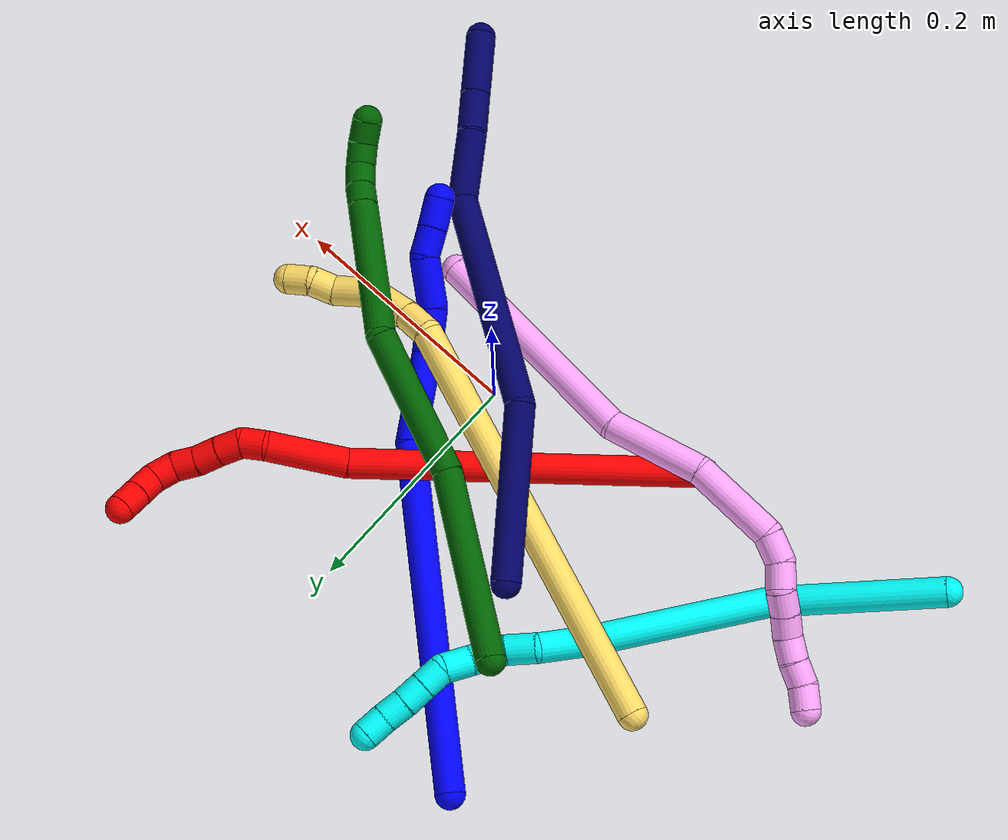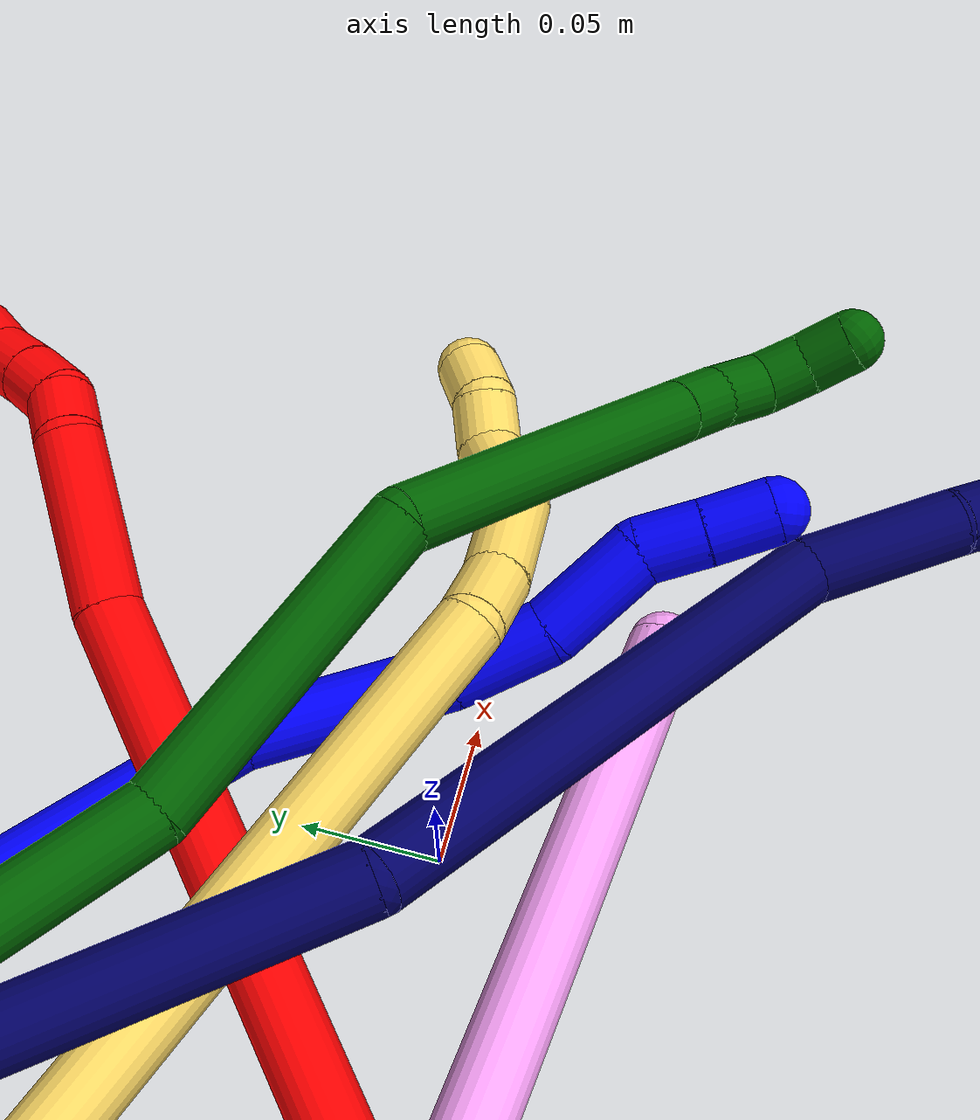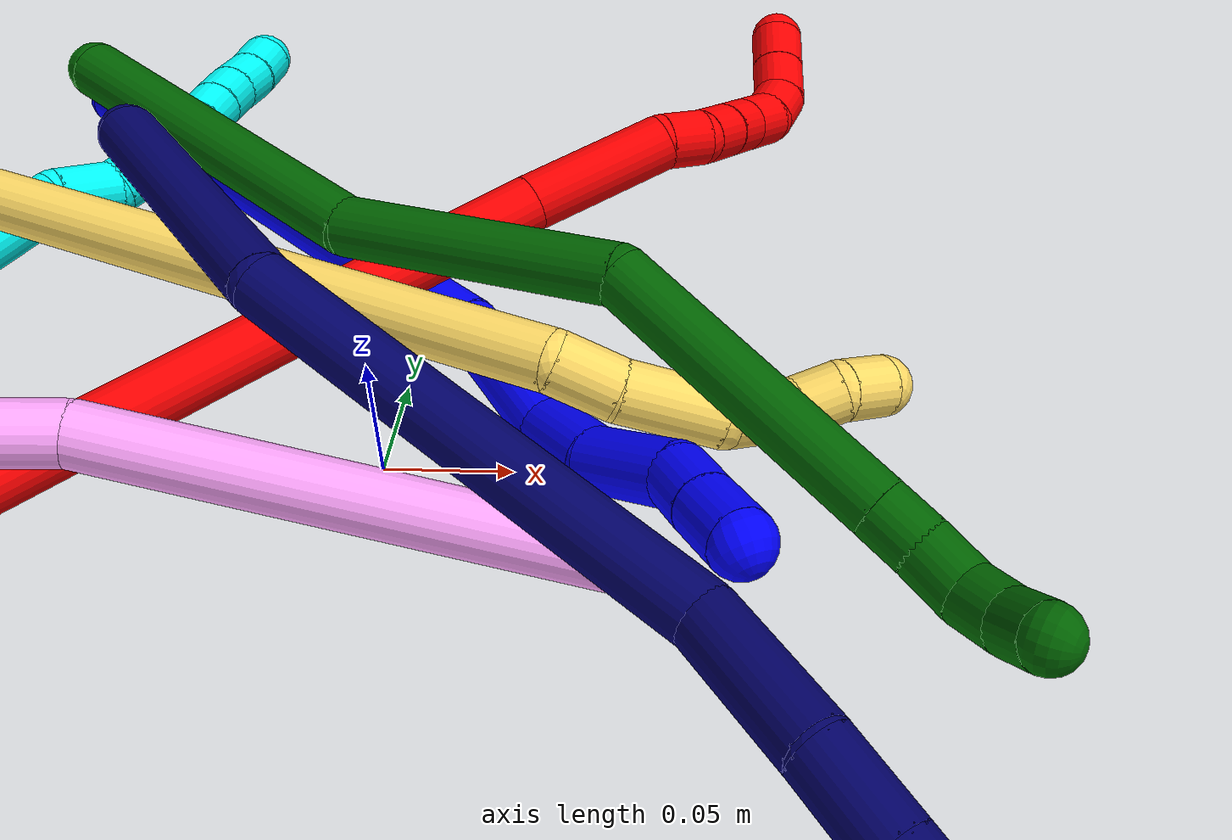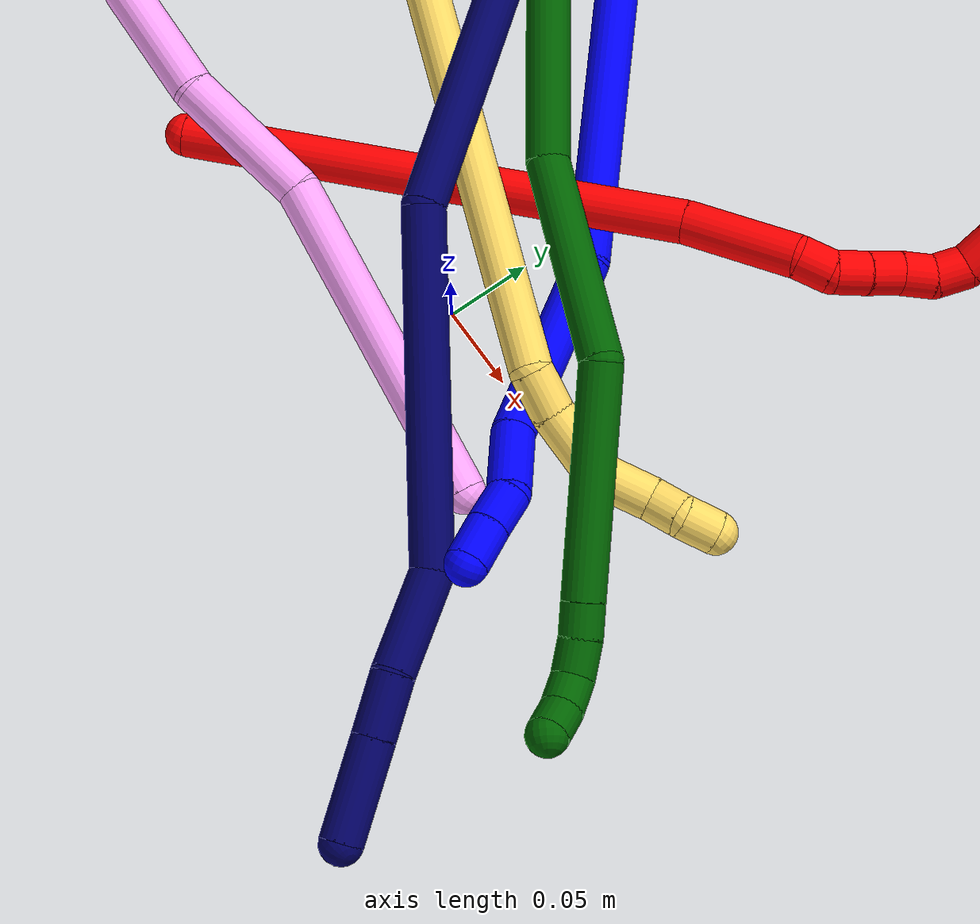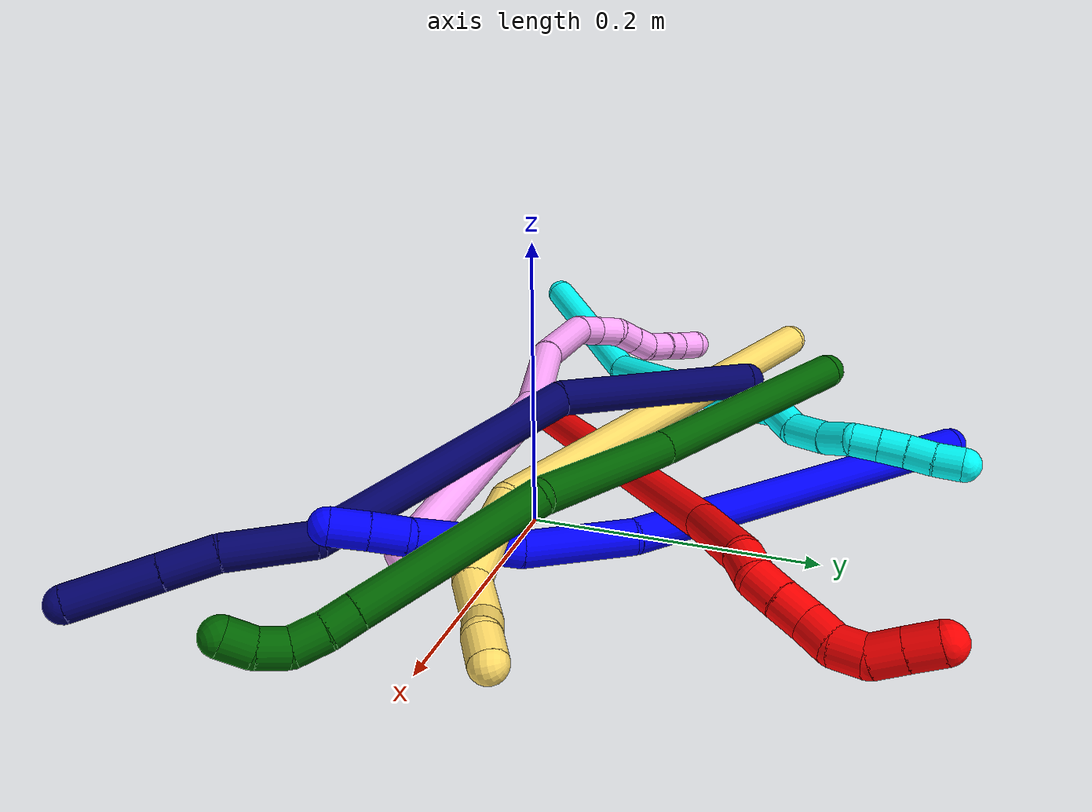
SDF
<sdf version="1.7">
 <world name="default">
  <plugin name="TubeGeneratorPlugin" filename="libtube_generator_plugin.so"/>
  <model name="photoneo_s_sensor">
   <static>1</static>
   <pose>0 0 2 1.57079 1.57079 3.14159</pose>
   <link name="link">
    <inertial><mass>0.1</mass></inertial>
    <sensor name="sensor" type="depth">
     <update_rate>30</update_rate>
     <camera>
      <horizontal_fov>1.22</horizontal_fov>
      <image><width>1920</width><height>1200</height><format>B8G8R8</format></image>
      <clip><near>0.1</near><far>4</far></clip>
      <depth_camera><output>points</output></depth_camera>
     </camera>
     <plugin name="camera_plugin" filename="libgazebo_ros_depth_camera.so">
      <baseline>0.2</baseline>
      <alwaysOn>1</alwaysOn>
      <updateRate>0.0</updateRate>
      <cameraName>camera_ir</cameraName>
      <imageTopicName>/camera/color/image_raw</imageTopicName>
      <cameraInfoTopicName>/camera/color/camera_info</cameraInfoTopicName>
      <depthImageTopicName>/camera/depth/image_raw</depthImageTopicName>
      <depthImageCameraInfoTopicName>/camera/depth/camera_info</depthImageCameraInfoTopicName>
      <pointCloudTopicName>/camera/depth/points</pointCloudTopicName>
      <frameName>fr_optical</frameName>
      <pointCloudCutoff>0.1</pointCloudCutoff>
      <pointCloudCutoffMax>2.0</pointCloudCutoffMax>
      <distortionK1>0</distortionK1>
      <distortionK2>0</distortionK2>
      <distortionK3>0</distortionK3>
      <distortionT1>0</distortionT1>
      <distortionT2>0</distortionT2>
      <CxPrime>0</CxPrime>
      <Cx>0</Cx>
      <Cy>0</Cy>
      <focalLength>0</focalLength>
      <hackBaseline>0</hackBaseline>
     </plugin>
    </sensor>
   </link>
  </model>
  <gravity>0 0 -9.8</gravity>
  <magnetic_field>6e-06 2.3e-05 -4.2e-05</magnetic_field>
  <atmosphere type="adiabatic"/>
  <physics name="default_physics" default="0" type="ode">
   <max_step_size>0.003</max_step_size>
   <real_time_factor>1</real_time_factor>
   <real_time_update_rate>1000</real_time_update_rate>
   <max_contacts>10000</max_contacts>
   <ode>
    <solver>
     <type>quick</type>
     <iters>100</iters>
     <sor>1.3</sor>
     <use_dynamic_moi_rescaling>0</use_dynamic_moi_rescaling>
    </solver>
    <constraints>
     <contact_max_correcting_vel>0</contact_max_correcting_vel>
     <contact_surface_layer>0.001</contact_surface_layer>
     <cfm>0</cfm>
     <erp>0.2</erp>
    </constraints>
   </ode>
  </physics>
  <scene><ambient>0.4 0.4 0.4 1</ambient><background>0.7 0.7 0.7 1</background><shadows>0</shadows></scene>
  <audio><device>default</device></audio>
  <spherical_coordinates>
   <surface_model>EARTH_WGS84</surface_model>
   <latitude_deg>0</latitude_deg>
   <longitude_deg>0</longitude_deg>
   <elevation>0</elevation>
   <heading_deg>0</heading_deg>
  </spherical_coordinates>
  <model name="bin">
   <static>1</static>
   <link name="bottom">
    <collision name="collision-bottom">
     <pose>0 0 -0.01 0 -0 0</pose>
     <geometry><box><size>0.8 0.6 0.02</size></box></geometry>
     <surface>
      <friction><ode><mu>100</mu><mu2>100</mu2></ode></friction>
      <contact><collide_bitmask>65535</collide_bitmask></contact>
     </surface>
    </collision>
   </link>
   <link name="west_wall">
    <collision name="collision-west_wall">
     <pose>-0.41 0 0.1 0 -0 0</pose>
     <geometry><box><size>0.02 0.6 0.2</size></box></geometry>
     <surface>
      <friction><ode><mu>100</mu><mu2>100</mu2></ode></friction>
      <contact><collide_bitmask>65535</collide_bitmask></contact>
     </surface>
    </collision>
   </link>
   <link name="east_wall">
    <collision name="collision-east_wall">
     <pose>0.41 0 0.1 0 -0 0</pose>
     <geometry><box><size>0.02 0.6 0.2</size></box></geometry>
     <surface>
      <friction><ode><mu>100</mu><mu2>100</mu2></ode></friction>
      <contact><collide_bitmask>65535</collide_bitmask></contact>
     </surface>
    </collision>
   </link>
   <link name="south_wall">
    <collision name="collision-south_wall">
     <pose>0 -0.31 0.1 0 -0 0</pose>
     <geometry><box><size>0.8 0.02 0.2</size></box></geometry>
     <surface>
      <friction><ode><mu>100</mu><mu2>100</mu2></ode></friction>
      <contact><collide_bitmask>65535</collide_bitmask></contact>
     </surface>
    </collision>
   </link>
   <link name="north_wall">
    <collision name="collision-north_wall">
     <pose>0 0.31 0.1 0 -0 0</pose>
     <geometry><box><size>0.8 0.02 0.2</size></box></geometry>
     <surface>
      <friction><ode><mu>100</mu><mu2>100</mu2></ode></friction>
      <contact><collide_bitmask>65535</collide_bitmask></contact>
     </surface>
    </collision>
   </link>
  </model>
  <model name="1">
   <static>0</static>
   <link name="1">
    <collision name="collision-cylinder-e_1_1_4">
     <pose>0.058145 -0.059407 -0.119839 2.68138 0.410069 1.45199</pose>
     <geometry><cylinder><radius>0.0125</radius><length>0.291695</length></cylinder></geometry>
     <surface>
      <friction><ode><mu>1.16</mu><mu2>1.16</mu2><slip1>0</slip1><slip2>0</slip2></ode></friction>
      <contact><ode><kp>1e+06</kp><kd>1</kd><max_vel>0</max_vel><min_depth>0.001</min_depth></ode></contact>
     </surface>
    </collision>
    <visual name="visual-cylinder-e_1_1_4">
     <pose>0.058145 -0.059407 -0.119839 2.68138 0.410069 1.45199</pose>
     <geometry><cylinder><radius>0.0125</radius><length>0.291695</length></cylinder></geometry>
     <material><ambient>0 0 1 1</ambient></material>
    </visual>
    <collision name="collision-cylinder-e_2_4_5">
     <pose>0.120999 -0.136488 -0.273508 2.66012 0.122727 0.490467</pose>
     <geometry><cylinder><radius>0.0125</radius><length>0.076916</length></cylinder></geometry>
     <surface>
      <friction><ode><mu>1.16</mu><mu2>1.16</mu2><slip1>0</slip1><slip2>0</slip2></ode></friction>
      <contact><ode><kp>1e+06</kp><kd>1</kd><max_vel>0</max_vel><min_depth>0.001</min_depth></ode></contact>
     </surface>
    </collision>
    <visual name="visual-cylinder-e_2_4_5">
     <pose>0.120999 -0.136488 -0.273508 2.66012 0.122727 0.490467</pose>
     <geometry><cylinder><radius>0.0125</radius><length>0.076916</length></cylinder></geometry>
     <material><ambient>0 0 1 1</ambient></material>
    </visual>
    <collision name="collision-cylinder-e_3_5_6">
     <pose>0.128902 -0.167511 -0.321048 2.36965 0.165443 0.402545</pose>
     <geometry><cylinder><radius>0.0125</radius><length>0.0388</length></cylinder></geometry>
     <surface>
      <friction><ode><mu>1.16</mu><mu2>1.16</mu2><slip1>0</slip1><slip2>0</slip2></ode></friction>
      <contact><ode><kp>1e+06</kp><kd>1</kd><max_vel>0</max_vel><min_depth>0.001</min_depth></ode></contact>
     </surface>
    </collision>
    <visual name="visual-cylinder-e_3_5_6">
     <pose>0.128902 -0.167511 -0.321048 2.36965 0.165443 0.402545</pose>
     <geometry><cylinder><radius>0.0125</radius><length>0.0388</length></cylinder></geometry>
     <material><ambient>0 0 1 1</ambient></material>
    </visual>
    <collision name="collision-cylinder-e_4_6_7">
     <pose>0.141171 -0.195801 -0.347118 2.26179 0.437687 0.882881</pose>
     <geometry><cylinder><radius>0.0125</radius><length>0.04282</length></cylinder></geometry>
     <surface>
      <friction><ode><mu>1.16</mu><mu2>1.16</mu2><slip1>0</slip1><slip2>0</slip2></ode></friction>
      <contact><ode><kp>1e+06</kp><kd>1</kd><max_vel>0</max_vel><min_depth>0.001</min_depth></ode></contact>
     </surface>
    </collision>
    <visual name="visual-cylinder-e_4_6_7">
     <pose>0.141171 -0.195801 -0.347118 2.26179 0.437687 0.882881</pose>
     <geometry><cylinder><radius>0.0125</radius><length>0.04282</length></cylinder></geometry>
     <material><ambient>0 0 1 1</ambient></material>
    </visual>
    <collision name="collision-cylinder-e_5_7_8">
     <pose>0.150469 -0.218682 -0.368611 2.42621 0.01848 0.049435</pose>
     <geometry><cylinder><radius>0.0125</radius><length>0.024206</length></cylinder></geometry>
     <surface>
      <friction><ode><mu>1.16</mu><mu2>1.16</mu2><slip1>0</slip1><slip2>0</slip2></ode></friction>
      <contact><ode><kp>1e+06</kp><kd>1</kd><max_vel>0</max_vel><min_depth>0.001</min_depth></ode></contact>
     </surface>
    </collision>
    <visual name="visual-cylinder-e_5_7_8">
     <pose>0.150469 -0.218682 -0.368611 2.42621 0.01848 0.049435</pose>
     <geometry><cylinder><radius>0.0125</radius><length>0.024206</length></cylinder></geometry>
     <material><ambient>0 0 1 1</ambient></material>
    </visual>
    <collision name="collision-cylinder-e_6_8_2">
     <pose>0.151426 -0.234846 -0.3875 2.44093 0.057363 0.156707</pose>
     <geometry><cylinder><radius>0.0125</radius><length>0.025565</length></cylinder></geometry>
     <surface>
      <friction><ode><mu>1.16</mu><mu2>1.16</mu2><slip1>0</slip1><slip2>0</slip2></ode></friction>
      <contact><ode><kp>1e+06</kp><kd>1</kd><max_vel>0</max_vel><min_depth>0.001</min_depth></ode></contact>
     </surface>
    </collision>
    <visual name="visual-cylinder-e_6_8_2">
     <pose>0.151426 -0.234846 -0.3875 2.44093 0.057363 0.156707</pose>
     <geometry><cylinder><radius>0.0125</radius><length>0.025565</length></cylinder></geometry>
     <material><ambient>0 0 1 1</ambient></material>
    </visual>
    <collision name="collision-sphere-2">
     <pose>0.152158 -0.243074 -0.397255 0 -0 0</pose>
     <geometry><sphere><radius>0.0125</radius></sphere></geometry>
     <surface>
      <friction><ode><mu>1.16</mu><mu2>1.16</mu2><slip1>0</slip1><slip2>0</slip2></ode></friction>
      <contact><ode><kp>1e+06</kp><kd>1</kd><max_vel>0</max_vel><min_depth>0.001</min_depth></ode></contact>
     </surface>
    </collision>
    <visual name="visual-sphere-2">
     <pose>0.152158 -0.243074 -0.397255 0 -0 0</pose>
     <geometry><sphere><radius>0.0125</radius></sphere></geometry>
     <material><ambient>0 0 1 1</ambient></material>
    </visual>
    <collision name="collision-sphere-4">
     <pose>0.116291 -0.118813 -0.239678 0 -0 0</pose>
     <geometry><sphere><radius>0.0125</radius></sphere></geometry>
     <surface>
      <friction><ode><mu>1.16</mu><mu2>1.16</mu2><slip1>0</slip1><slip2>0</slip2></ode></friction>
      <contact><ode><kp>1e+06</kp><kd>1</kd><max_vel>0</max_vel><min_depth>0.001</min_depth></ode></contact>
     </surface>
    </collision>
    <visual name="visual-sphere-4">
     <pose>0.116291 -0.118813 -0.239678 0 -0 0</pose>
     <geometry><sphere><radius>0.0125</radius></sphere></geometry>
     <material><ambient>0 0 1 1</ambient></material>
    </visual>
    <collision name="collision-sphere-1">
     <geometry><sphere><radius>0.0125</radius></sphere></geometry>
     <surface>
      <friction><ode><mu>1.16</mu><mu2>1.16</mu2><slip1>0</slip1><slip2>0</slip2></ode></friction>
      <contact><ode><kp>1e+06</kp><kd>1</kd><max_vel>0</max_vel><min_depth>0.001</min_depth></ode></contact>
     </surface>
    </collision>
    <visual name="visual-sphere-1">
     <geometry><sphere><radius>0.0125</radius></sphere></geometry>
     <material><ambient>0 0 1 1</ambient></material>
    </visual>
    <collision name="collision-sphere-8">
     <pose>0.150693 -0.226619 -0.377745 0 -0 0</pose>
     <geometry><sphere><radius>0.0125</radius></sphere></geometry>
     <surface>
      <friction><ode><mu>1.16</mu><mu2>1.16</mu2><slip1>0</slip1><slip2>0</slip2></ode></friction>
      <contact><ode><kp>1e+06</kp><kd>1</kd><max_vel>0</max_vel><min_depth>0.001</min_depth></ode></contact>
     </surface>
    </collision>
    <visual name="visual-sphere-8">
     <pose>0.150693 -0.226619 -0.377745 0 -0 0</pose>
     <geometry><sphere><radius>0.0125</radius></sphere></geometry>
     <material><ambient>0 0 1 1</ambient></material>
    </visual>
    <collision name="collision-sphere-5">
     <pose>0.125707 -0.154164 -0.307337 0 -0 0</pose>
     <geometry><sphere><radius>0.0125</radius></sphere></geometry>
     <surface>
      <friction><ode><mu>1.16</mu><mu2>1.16</mu2><slip1>0</slip1><slip2>0</slip2></ode></friction>
      <contact><ode><kp>1e+06</kp><kd>1</kd><max_vel>0</max_vel><min_depth>0.001</min_depth></ode></contact>
     </surface>
    </collision>
    <visual name="visual-sphere-5">
     <pose>0.125707 -0.154164 -0.307337 0 -0 0</pose>
     <geometry><sphere><radius>0.0125</radius></sphere></geometry>
     <material><ambient>0 0 1 1</ambient></material>
    </visual>
    <collision name="collision-sphere-6">
     <pose>0.132096 -0.180858 -0.33476 0 -0 0</pose>
     <geometry><sphere><radius>0.0125</radius></sphere></geometry>
     <surface>
      <friction><ode><mu>1.16</mu><mu2>1.16</mu2><slip1>0</slip1><slip2>0</slip2></ode></friction>
      <contact><ode><kp>1e+06</kp><kd>1</kd><max_vel>0</max_vel><min_depth>0.001</min_depth></ode></contact>
     </surface>
    </collision>
    <visual name="visual-sphere-6">
     <pose>0.132096 -0.180858 -0.33476 0 -0 0</pose>
     <geometry><sphere><radius>0.0125</radius></sphere></geometry>
     <material><ambient>0 0 1 1</ambient></material>
    </visual>
    <collision name="collision-sphere-7">
     <pose>0.150245 -0.210745 -0.359476 0 -0 0</pose>
     <geometry><sphere><radius>0.0125</radius></sphere></geometry>
     <surface>
      <friction><ode><mu>1.16</mu><mu2>1.16</mu2><slip1>0</slip1><slip2>0</slip2></ode></friction>
      <contact><ode><kp>1e+06</kp><kd>1</kd><max_vel>0</max_vel><min_depth>0.001</min_depth></ode></contact>
     </surface>
    </collision>
    <visual name="visual-sphere-7">
     <pose>0.150245 -0.210745 -0.359476 0 -0 0</pose>
     <geometry><sphere><radius>0.0125</radius></sphere></geometry>
     <material><ambient>0 0 1 1</ambient></material>
    </visual>
    <inertial>
     <pose>0.089654 -0.108015 -0.204285 0 -0 0</pose>
     <mass>0.5</mass>
     <inertia><ixx>0.00221</ixx><ixy>0</ixy><ixz>0</ixz><iyy>0.002008</iyy><iyz>0</iyz><izz>9e-06</izz></inertia>
    </inertial>
   </link>
   <pose>-0.197087 0.271285 0.014515 -1.08537 -0.031761 0.439058</pose>
  </model>
  <model name="2">
   <static>0</static>
   <link name="2">
    <collision name="collision-cylinder-e_1_1_4">
     <pose>0.023955 0.047916 0.135884 -0.339013 0.164749 -0.028259</pose>
     <geometry><cylinder><radius>0.0125</radius><length>0.292125</length></cylinder></geometry>
     <surface>
      <friction><ode><mu>1.16</mu><mu2>1.16</mu2><slip1>0</slip1><slip2>0</slip2></ode></friction>
      <contact><ode><kp>1e+06</kp><kd>1</kd><max_vel>0</max_vel><min_depth>0.001</min_depth></ode></contact>
     </surface>
    </collision>
    <visual name="visual-cylinder-e_1_1_4">
     <pose>0.023955 0.047916 0.135884 -0.339013 0.164749 -0.028259</pose>
     <geometry><cylinder><radius>0.0125</radius><length>0.292125</length></cylinder></geometry>
     <material><ambient>1 0 0 1</ambient></material>
    </visual>
    <collision name="collision-cylinder-e_2_4_5">
     <pose>0.049899 0.101938 0.30472 -0.183202 0.059283 -0.005447</pose>
     <geometry><cylinder><radius>0.0125</radius><length>0.067144</length></cylinder></geometry>
     <surface>
      <friction><ode><mu>1.16</mu><mu2>1.16</mu2><slip1>0</slip1><slip2>0</slip2></ode></friction>
      <contact><ode><kp>1e+06</kp><kd>1</kd><max_vel>0</max_vel><min_depth>0.001</min_depth></ode></contact>
     </surface>
    </collision>
    <visual name="visual-cylinder-e_2_4_5">
     <pose>0.049899 0.101938 0.30472 -0.183202 0.059283 -0.005447</pose>
     <geometry><cylinder><radius>0.0125</radius><length>0.067144</length></cylinder></geometry>
     <material><ambient>1 0 0 1</ambient></material>
    </visual>
    <collision name="collision-cylinder-e_3_5_6">
     <pose>0.055781 0.10919 0.346941 -0.123116 0.394961 -0.024664</pose>
     <geometry><cylinder><radius>0.0125</radius><length>0.020237</length></cylinder></geometry>
     <surface>
      <friction><ode><mu>1.16</mu><mu2>1.16</mu2><slip1>0</slip1><slip2>0</slip2></ode></friction>
      <contact><ode><kp>1e+06</kp><kd>1</kd><max_vel>0</max_vel><min_depth>0.001</min_depth></ode></contact>
     </surface>
    </collision>
    <visual name="visual-cylinder-e_3_5_6">
     <pose>0.055781 0.10919 0.346941 -0.123116 0.394961 -0.024664</pose>
     <geometry><cylinder><radius>0.0125</radius><length>0.020237</length></cylinder></geometry>
     <material><ambient>1 0 0 1</ambient></material>
    </visual>
    <collision name="collision-cylinder-e_4_6_7">
     <pose>0.065117 0.115362 0.363224 -0.621594 0.562742 -0.185152</pose>
     <geometry><cylinder><radius>0.0125</radius><length>0.020403</length></cylinder></geometry>
     <surface>
      <friction><ode><mu>1.16</mu><mu2>1.16</mu2><slip1>0</slip1><slip2>0</slip2></ode></friction>
      <contact><ode><kp>1e+06</kp><kd>1</kd><max_vel>0</max_vel><min_depth>0.001</min_depth></ode></contact>
     </surface>
    </collision>
    <visual name="visual-cylinder-e_4_6_7">
     <pose>0.065117 0.115362 0.363224 -0.621594 0.562742 -0.185152</pose>
     <geometry><cylinder><radius>0.0125</radius><length>0.020403</length></cylinder></geometry>
     <material><ambient>1 0 0 1</ambient></material>
    </visual>
    <collision name="collision-cylinder-e_5_7_8">
     <pose>0.076149 0.125668 0.376649 -0.6891 0.592285 -0.218121</pose>
     <geometry><cylinder><radius>0.0125</radius><length>0.020022</length></cylinder></geometry>
     <surface>
      <friction><ode><mu>1.16</mu><mu2>1.16</mu2><slip1>0</slip1><slip2>0</slip2></ode></friction>
      <contact><ode><kp>1e+06</kp><kd>1</kd><max_vel>0</max_vel><min_depth>0.001</min_depth></ode></contact>
     </surface>
    </collision>
    <visual name="visual-cylinder-e_5_7_8">
     <pose>0.076149 0.125668 0.376649 -0.6891 0.592285 -0.218121</pose>
     <geometry><cylinder><radius>0.0125</radius><length>0.020022</length></cylinder></geometry>
     <material><ambient>1 0 0 1</ambient></material>
    </visual>
    <collision name="collision-cylinder-e_6_8_9">
     <pose>0.08655 0.135255 0.390735 -0.511329 0.500388 -0.133395</pose>
     <geometry><cylinder><radius>0.0125</radius><length>0.02006</length></cylinder></geometry>
     <surface>
      <friction><ode><mu>1.16</mu><mu2>1.16</mu2><slip1>0</slip1><slip2>0</slip2></ode></friction>
      <contact><ode><kp>1e+06</kp><kd>1</kd><max_vel>0</max_vel><min_depth>0.001</min_depth></ode></contact>
     </surface>
    </collision>
    <visual name="visual-cylinder-e_6_8_9">
     <pose>0.08655 0.135255 0.390735 -0.511329 0.500388 -0.133395</pose>
     <geometry><cylinder><radius>0.0125</radius><length>0.02006</length></cylinder></geometry>
     <material><ambient>1 0 0 1</ambient></material>
    </visual>
    <collision name="collision-cylinder-e_7_9_10">
     <pose>0.093968 0.147015 0.404547 -0.881895 0.263621 -0.124975</pose>
     <geometry><cylinder><radius>0.0125</radius><length>0.020001</length></cylinder></geometry>
     <surface>
      <friction><ode><mu>1.16</mu><mu2>1.16</mu2><slip1>0</slip1><slip2>0</slip2></ode></friction>
      <contact><ode><kp>1e+06</kp><kd>1</kd><max_vel>0</max_vel><min_depth>0.001</min_depth></ode></contact>
     </surface>
    </collision>
    <visual name="visual-cylinder-e_7_9_10">
     <pose>0.093968 0.147015 0.404547 -0.881895 0.263621 -0.124975</pose>
     <geometry><cylinder><radius>0.0125</radius><length>0.020001</length></cylinder></geometry>
     <material><ambient>1 0 0 1</ambient></material>
    </visual>
    <collision name="collision-cylinder-e_8_10_11">
     <pose>0.095185 0.163699 0.414278 -1.19955 -0.139257 0.095307</pose>
     <geometry><cylinder><radius>0.0125</radius><length>0.020006</length></cylinder></geometry>
     <surface>
      <friction><ode><mu>1.16</mu><mu2>1.16</mu2><slip1>0</slip1><slip2>0</slip2></ode></friction>
      <contact><ode><kp>1e+06</kp><kd>1</kd><max_vel>0</max_vel><min_depth>0.001</min_depth></ode></contact>
     </surface>
    </collision>
    <visual name="visual-cylinder-e_8_10_11">
     <pose>0.095185 0.163699 0.414278 -1.19955 -0.139257 0.095307</pose>
     <geometry><cylinder><radius>0.0125</radius><length>0.020006</length></cylinder></geometry>
     <material><ambient>1 0 0 1</ambient></material>
    </visual>
    <collision name="collision-cylinder-e_9_11_2">
     <pose>0.09255 0.182136 0.421575 -1.18835 -0.125003 0.084514</pose>
     <geometry><cylinder><radius>0.0125</radius><length>0.020002</length></cylinder></geometry>
     <surface>
      <friction><ode><mu>1.16</mu><mu2>1.16</mu2><slip1>0</slip1><slip2>0</slip2></ode></friction>
      <contact><ode><kp>1e+06</kp><kd>1</kd><max_vel>0</max_vel><min_depth>0.001</min_depth></ode></contact>
     </surface>
    </collision>
    <visual name="visual-cylinder-e_9_11_2">
     <pose>0.09255 0.182136 0.421575 -1.18835 -0.125003 0.084514</pose>
     <geometry><cylinder><radius>0.0125</radius><length>0.020002</length></cylinder></geometry>
     <material><ambient>1 0 0 1</ambient></material>
    </visual>
    <collision name="collision-sphere-2">
     <pose>0.091303 0.191342 0.425278 0 -0 0</pose>
     <geometry><sphere><radius>0.0125</radius></sphere></geometry>
     <surface>
      <friction><ode><mu>1.16</mu><mu2>1.16</mu2><slip1>0</slip1><slip2>0</slip2></ode></friction>
      <contact><ode><kp>1e+06</kp><kd>1</kd><max_vel>0</max_vel><min_depth>0.001</min_depth></ode></contact>
     </surface>
    </collision>
    <visual name="visual-sphere-2">
     <pose>0.091303 0.191342 0.425278 0 -0 0</pose>
     <geometry><sphere><radius>0.0125</radius></sphere></geometry>
     <material><ambient>1 0 0 1</ambient></material>
    </visual>
    <collision name="collision-sphere-11">
     <pose>0.093797 0.17293 0.417872 0 -0 0</pose>
     <geometry><sphere><radius>0.0125</radius></sphere></geometry>
     <surface>
      <friction><ode><mu>1.16</mu><mu2>1.16</mu2><slip1>0</slip1><slip2>0</slip2></ode></friction>
      <contact><ode><kp>1e+06</kp><kd>1</kd><max_vel>0</max_vel><min_depth>0.001</min_depth></ode></contact>
     </surface>
    </collision>
    <visual name="visual-sphere-11">
     <pose>0.093797 0.17293 0.417872 0 -0 0</pose>
     <geometry><sphere><radius>0.0125</radius></sphere></geometry>
     <material><ambient>1 0 0 1</ambient></material>
    </visual>
    <collision name="collision-sphere-10">
     <pose>0.096574 0.154468 0.410685 0 -0 0</pose>
     <geometry><sphere><radius>0.0125</radius></sphere></geometry>
     <surface>
      <friction><ode><mu>1.16</mu><mu2>1.16</mu2><slip1>0</slip1><slip2>0</slip2></ode></friction>
      <contact><ode><kp>1e+06</kp><kd>1</kd><max_vel>0</max_vel><min_depth>0.001</min_depth></ode></contact>
     </surface>
    </collision>
    <visual name="visual-sphere-10">
     <pose>0.096574 0.154468 0.410685 0 -0 0</pose>
     <geometry><sphere><radius>0.0125</radius></sphere></geometry>
     <material><ambient>1 0 0 1</ambient></material>
    </visual>
    <collision name="collision-sphere-9">
     <pose>0.091362 0.139562 0.39841 0 -0 0</pose>
     <geometry><sphere><radius>0.0125</radius></sphere></geometry>
     <surface>
      <friction><ode><mu>1.16</mu><mu2>1.16</mu2><slip1>0</slip1><slip2>0</slip2></ode></friction>
      <contact><ode><kp>1e+06</kp><kd>1</kd><max_vel>0</max_vel><min_depth>0.001</min_depth></ode></contact>
     </surface>
    </collision>
    <visual name="visual-sphere-9">
     <pose>0.091362 0.139562 0.39841 0 -0 0</pose>
     <geometry><sphere><radius>0.0125</radius></sphere></geometry>
     <material><ambient>1 0 0 1</ambient></material>
    </visual>
    <collision name="collision-sphere-4">
     <pose>0.04791 0.095833 0.271768 0 -0 0</pose>
     <geometry><sphere><radius>0.0125</radius></sphere></geometry>
     <surface>
      <friction><ode><mu>1.16</mu><mu2>1.16</mu2><slip1>0</slip1><slip2>0</slip2></ode></friction>
      <contact><ode><kp>1e+06</kp><kd>1</kd><max_vel>0</max_vel><min_depth>0.001</min_depth></ode></contact>
     </surface>
    </collision>
    <visual name="visual-sphere-4">
     <pose>0.04791 0.095833 0.271768 0 -0 0</pose>
     <geometry><sphere><radius>0.0125</radius></sphere></geometry>
     <material><ambient>1 0 0 1</ambient></material>
    </visual>
    <collision name="collision-sphere-1">
     <geometry><sphere><radius>0.0125</radius></sphere></geometry>
     <surface>
      <friction><ode><mu>1.16</mu><mu2>1.16</mu2><slip1>0</slip1><slip2>0</slip2></ode></friction>
      <contact><ode><kp>1e+06</kp><kd>1</kd><max_vel>0</max_vel><min_depth>0.001</min_depth></ode></contact>
     </surface>
    </collision>
    <visual name="visual-sphere-1">
     <geometry><sphere><radius>0.0125</radius></sphere></geometry>
     <material><ambient>1 0 0 1</ambient></material>
    </visual>
    <collision name="collision-sphere-8">
     <pose>0.081737 0.130949 0.38306 0 -0 0</pose>
     <geometry><sphere><radius>0.0125</radius></sphere></geometry>
     <surface>
      <friction><ode><mu>1.16</mu><mu2>1.16</mu2><slip1>0</slip1><slip2>0</slip2></ode></friction>
      <contact><ode><kp>1e+06</kp><kd>1</kd><max_vel>0</max_vel><min_depth>0.001</min_depth></ode></contact>
     </surface>
    </collision>
    <visual name="visual-sphere-8">
     <pose>0.081737 0.130949 0.38306 0 -0 0</pose>
     <geometry><sphere><radius>0.0125</radius></sphere></geometry>
     <material><ambient>1 0 0 1</ambient></material>
    </visual>
    <collision name="collision-sphere-5">
     <pose>0.051888 0.108043 0.337672 0 -0 0</pose>
     <geometry><sphere><radius>0.0125</radius></sphere></geometry>
     <surface>
      <friction><ode><mu>1.16</mu><mu2>1.16</mu2><slip1>0</slip1><slip2>0</slip2></ode></friction>
      <contact><ode><kp>1e+06</kp><kd>1</kd><max_vel>0</max_vel><min_depth>0.001</min_depth></ode></contact>
     </surface>
    </collision>
    <visual name="visual-sphere-5">
     <pose>0.051888 0.108043 0.337672 0 -0 0</pose>
     <geometry><sphere><radius>0.0125</radius></sphere></geometry>
     <material><ambient>1 0 0 1</ambient></material>
    </visual>
    <collision name="collision-sphere-6">
     <pose>0.059675 0.110337 0.35621 0 -0 0</pose>
     <geometry><sphere><radius>0.0125</radius></sphere></geometry>
     <surface>
      <friction><ode><mu>1.16</mu><mu2>1.16</mu2><slip1>0</slip1><slip2>0</slip2></ode></friction>
      <contact><ode><kp>1e+06</kp><kd>1</kd><max_vel>0</max_vel><min_depth>0.001</min_depth></ode></contact>
     </surface>
    </collision>
    <visual name="visual-sphere-6">
     <pose>0.059675 0.110337 0.35621 0 -0 0</pose>
     <geometry><sphere><radius>0.0125</radius></sphere></geometry>
     <material><ambient>1 0 0 1</ambient></material>
    </visual>
    <collision name="collision-sphere-7">
     <pose>0.07056 0.120386 0.370239 0 -0 0</pose>
     <geometry><sphere><radius>0.0125</radius></sphere></geometry>
     <surface>
      <friction><ode><mu>1.16</mu><mu2>1.16</mu2><slip1>0</slip1><slip2>0</slip2></ode></friction>
      <contact><ode><kp>1e+06</kp><kd>1</kd><max_vel>0</max_vel><min_depth>0.001</min_depth></ode></contact>
     </surface>
    </collision>
    <visual name="visual-sphere-7">
     <pose>0.07056 0.120386 0.370239 0 -0 0</pose>
     <geometry><sphere><radius>0.0125</radius></sphere></geometry>
     <material><ambient>1 0 0 1</ambient></material>
    </visual>
    <inertial>
     <pose>0.043403 0.080987 0.229557 0 -0 0</pose>
     <mass>0.5</mass>
     <inertia>
      <ixx>0.002045</ixx>
      <ixy>0</ixy>
      <ixz>0</ixz>
      <iyy>0.001963</iyy>
      <iyz>0</iyz>
      <izz>-0.00101</izz>
     </inertia>
    </inertial>
   </link>
   <pose>-0.173909 -0.063453 0.011496 0.78545 1.27582 1.16998</pose>
  </model>
  <model name="3">
   <static>0</static>
   <link name="3">
    <collision name="collision-cylinder-e_1_1_4">
     <pose>0.016011 0.053518 -0.044708 -2.26674 0.225691 -0.475509</pose>
     <geometry><cylinder><radius>0.0125</radius><length>0.143099</length></cylinder></geometry>
     <surface>
      <friction><ode><mu>1.16</mu><mu2>1.16</mu2><slip1>0</slip1><slip2>0</slip2></ode></friction>
      <contact><ode><kp>1e+06</kp><kd>1</kd><max_vel>0</max_vel><min_depth>0.001</min_depth></ode></contact>
     </surface>
    </collision>
    <visual name="visual-cylinder-e_1_1_4">
     <pose>0.016011 0.053518 -0.044708 -2.26674 0.225691 -0.475509</pose>
     <geometry><cylinder><radius>0.0125</radius><length>0.143099</length></cylinder></geometry>
     <material><ambient>0.003922 1 0.996078 1</ambient></material>
    </visual>
    <collision name="collision-cylinder-e_2_4_5">
     <pose>0.070603 0.144573 -0.144442 -2.54294 0.524975 -1.43275</pose>
     <geometry><cylinder><radius>0.0125</radius><length>0.153953</length></cylinder></geometry>
     <surface>
      <friction><ode><mu>1.16</mu><mu2>1.16</mu2><slip1>0</slip1><slip2>0</slip2></ode></friction>
      <contact><ode><kp>1e+06</kp><kd>1</kd><max_vel>0</max_vel><min_depth>0.001</min_depth></ode></contact>
     </surface>
    </collision>
    <visual name="visual-cylinder-e_2_4_5">
     <pose>0.070603 0.144573 -0.144442 -2.54294 0.524975 -1.43275</pose>
     <geometry><cylinder><radius>0.0125</radius><length>0.153953</length></cylinder></geometry>
     <material><ambient>0.003922 1 0.996078 1</ambient></material>
    </visual>
    <collision name="collision-cylinder-e_3_5_6">
     <pose>0.118985 0.190464 -0.21586 -2.67028 0.489572 -1.61029</pose>
     <geometry><cylinder><radius>0.0125</radius><length>0.041691</length></cylinder></geometry>
     <surface>
      <friction><ode><mu>1.16</mu><mu2>1.16</mu2><slip1>0</slip1><slip2>0</slip2></ode></friction>
      <contact><ode><kp>1e+06</kp><kd>1</kd><max_vel>0</max_vel><min_depth>0.001</min_depth></ode></contact>
     </surface>
    </collision>
    <visual name="visual-cylinder-e_3_5_6">
     <pose>0.118985 0.190464 -0.21586 -2.67028 0.489572 -1.61029</pose>
     <geometry><cylinder><radius>0.0125</radius><length>0.041691</length></cylinder></geometry>
     <material><ambient>0.003922 1 0.996078 1</ambient></material>
    </visual>
    <collision name="collision-cylinder-e_4_6_7">
     <pose>0.131884 0.208572 -0.240618 -2.27976 0.236391 -0.505555</pose>
     <geometry><cylinder><radius>0.0125</radius><length>0.026438</length></cylinder></geometry>
     <surface>
      <friction><ode><mu>1.16</mu><mu2>1.16</mu2><slip1>0</slip1><slip2>0</slip2></ode></friction>
      <contact><ode><kp>1e+06</kp><kd>1</kd><max_vel>0</max_vel><min_depth>0.001</min_depth></ode></contact>
     </surface>
    </collision>
    <visual name="visual-cylinder-e_4_6_7">
     <pose>0.131884 0.208572 -0.240618 -2.27976 0.236391 -0.505555</pose>
     <geometry><cylinder><radius>0.0125</radius><length>0.026438</length></cylinder></geometry>
     <material><ambient>0.003922 1 0.996078 1</ambient></material>
    </visual>
    <collision name="collision-cylinder-e_5_7_8">
     <pose>0.143491 0.225645 -0.25895 -2.5081 0.602899 -1.51803</pose>
     <geometry><cylinder><radius>0.0125</radius><length>0.030021</length></cylinder></geometry>
     <surface>
      <friction><ode><mu>1.16</mu><mu2>1.16</mu2><slip1>0</slip1><slip2>0</slip2></ode></friction>
      <contact><ode><kp>1e+06</kp><kd>1</kd><max_vel>0</max_vel><min_depth>0.001</min_depth></ode></contact>
     </surface>
    </collision>
    <visual name="visual-cylinder-e_5_7_8">
     <pose>0.143491 0.225645 -0.25895 -2.5081 0.602899 -1.51803</pose>
     <geometry><cylinder><radius>0.0125</radius><length>0.030021</length></cylinder></geometry>
     <material><ambient>0.003922 1 0.996078 1</ambient></material>
    </visual>
    <collision name="collision-cylinder-e_6_8_9">
     <pose>0.159396 0.236903 -0.277741 -2.72181 0.653045 -2.01855</pose>
     <geometry><cylinder><radius>0.0125</radius><length>0.024337</length></cylinder></geometry>
     <surface>
      <friction><ode><mu>1.16</mu><mu2>1.16</mu2><slip1>0</slip1><slip2>0</slip2></ode></friction>
      <contact><ode><kp>1e+06</kp><kd>1</kd><max_vel>0</max_vel><min_depth>0.001</min_depth></ode></contact>
     </surface>
    </collision>
    <visual name="visual-cylinder-e_6_8_9">
     <pose>0.159396 0.236903 -0.277741 -2.72181 0.653045 -2.01855</pose>
     <geometry><cylinder><radius>0.0125</radius><length>0.024337</length></cylinder></geometry>
     <material><ambient>0.003922 1 0.996078 1</ambient></material>
    </visual>
    <collision name="collision-cylinder-e_7_9_10">
     <pose>0.175062 0.245749 -0.289624 -2.12803 0.960812 -1.50761</pose>
     <geometry><cylinder><radius>0.0125</radius><length>0.020185</length></cylinder></geometry>
     <surface>
      <friction><ode><mu>1.16</mu><mu2>1.16</mu2><slip1>0</slip1><slip2>0</slip2></ode></friction>
      <contact><ode><kp>1e+06</kp><kd>1</kd><max_vel>0</max_vel><min_depth>0.001</min_depth></ode></contact>
     </surface>
    </collision>
    <visual name="visual-cylinder-e_7_9_10">
     <pose>0.175062 0.245749 -0.289624 -2.12803 0.960812 -1.50761</pose>
     <geometry><cylinder><radius>0.0125</radius><length>0.020185</length></cylinder></geometry>
     <material><ambient>0.003922 1 0.996078 1</ambient></material>
    </visual>
    <collision name="collision-cylinder-e_8_10_11">
     <pose>0.191478 0.255765 -0.295645 -2.09637 0.943348 -1.44948</pose>
     <geometry><cylinder><radius>0.0125</radius><length>0.020119</length></cylinder></geometry>
     <surface>
      <friction><ode><mu>1.16</mu><mu2>1.16</mu2><slip1>0</slip1><slip2>0</slip2></ode></friction>
      <contact><ode><kp>1e+06</kp><kd>1</kd><max_vel>0</max_vel><min_depth>0.001</min_depth></ode></contact>
     </surface>
    </collision>
    <visual name="visual-cylinder-e_8_10_11">
     <pose>0.191478 0.255765 -0.295645 -2.09637 0.943348 -1.44948</pose>
     <geometry><cylinder><radius>0.0125</radius><length>0.020119</length></cylinder></geometry>
     <material><ambient>0.003922 1 0.996078 1</ambient></material>
    </visual>
    <collision name="collision-cylinder-e_9_11_12">
     <pose>0.207235 0.266366 -0.302123 -2.14019 0.862488 -1.39832</pose>
     <geometry><cylinder><radius>0.0125</radius><length>0.020048</length></cylinder></geometry>
     <surface>
      <friction><ode><mu>1.16</mu><mu2>1.16</mu2><slip1>0</slip1><slip2>0</slip2></ode></friction>
      <contact><ode><kp>1e+06</kp><kd>1</kd><max_vel>0</max_vel><min_depth>0.001</min_depth></ode></contact>
     </surface>
    </collision>
    <visual name="visual-cylinder-e_9_11_12">
     <pose>0.207235 0.266366 -0.302123 -2.14019 0.862488 -1.39832</pose>
     <geometry><cylinder><radius>0.0125</radius><length>0.020048</length></cylinder></geometry>
     <material><ambient>0.003922 1 0.996078 1</ambient></material>
    </visual>
    <collision name="collision-cylinder-e_10_12_2">
     <pose>0.223125 0.276506 -0.30895 -2.18967 0.967212 -1.58947</pose>
     <geometry><cylinder><radius>0.0125</radius><length>0.020108</length></cylinder></geometry>
     <surface>
      <friction><ode><mu>1.16</mu><mu2>1.16</mu2><slip1>0</slip1><slip2>0</slip2></ode></friction>
      <contact><ode><kp>1e+06</kp><kd>1</kd><max_vel>0</max_vel><min_depth>0.001</min_depth></ode></contact>
     </surface>
    </collision>
    <visual name="visual-cylinder-e_10_12_2">
     <pose>0.223125 0.276506 -0.30895 -2.18967 0.967212 -1.58947</pose>
     <geometry><cylinder><radius>0.0125</radius><length>0.020108</length></cylinder></geometry>
     <material><ambient>0.003922 1 0.996078 1</ambient></material>
    </visual>
    <collision name="collision-sphere-2">
     <pose>0.231403 0.281155 -0.31226 0 -0 0</pose>
     <geometry><sphere><radius>0.0125</radius></sphere></geometry>
     <surface>
      <friction><ode><mu>1.16</mu><mu2>1.16</mu2><slip1>0</slip1><slip2>0</slip2></ode></friction>
      <contact><ode><kp>1e+06</kp><kd>1</kd><max_vel>0</max_vel><min_depth>0.001</min_depth></ode></contact>
     </surface>
    </collision>
    <visual name="visual-sphere-2">
     <pose>0.231403 0.281155 -0.31226 0 -0 0</pose>
     <geometry><sphere><radius>0.0125</radius></sphere></geometry>
     <material><ambient>0.003922 1 0.996078 1</ambient></material>
    </visual>
    <collision name="collision-sphere-12">
     <pose>0.214848 0.271858 -0.305639 0 -0 0</pose>
     <geometry><sphere><radius>0.0125</radius></sphere></geometry>
     <surface>
      <friction><ode><mu>1.16</mu><mu2>1.16</mu2><slip1>0</slip1><slip2>0</slip2></ode></friction>
      <contact><ode><kp>1e+06</kp><kd>1</kd><max_vel>0</max_vel><min_depth>0.001</min_depth></ode></contact>
     </surface>
    </collision>
    <visual name="visual-sphere-12">
     <pose>0.214848 0.271858 -0.305639 0 -0 0</pose>
     <geometry><sphere><radius>0.0125</radius></sphere></geometry>
     <material><ambient>0.003922 1 0.996078 1</ambient></material>
    </visual>
    <collision name="collision-sphere-11">
     <pose>0.199622 0.260874 -0.298608 0 -0 0</pose>
     <geometry><sphere><radius>0.0125</radius></sphere></geometry>
     <surface>
      <friction><ode><mu>1.16</mu><mu2>1.16</mu2><slip1>0</slip1><slip2>0</slip2></ode></friction>
      <contact><ode><kp>1e+06</kp><kd>1</kd><max_vel>0</max_vel><min_depth>0.001</min_depth></ode></contact>
     </surface>
    </collision>
    <visual name="visual-sphere-11">
     <pose>0.199622 0.260874 -0.298608 0 -0 0</pose>
     <geometry><sphere><radius>0.0125</radius></sphere></geometry>
     <material><ambient>0.003922 1 0.996078 1</ambient></material>
    </visual>
    <collision name="collision-sphere-10">
     <pose>0.183334 0.250656 -0.292682 0 -0 0</pose>
     <geometry><sphere><radius>0.0125</radius></sphere></geometry>
     <surface>
      <friction><ode><mu>1.16</mu><mu2>1.16</mu2><slip1>0</slip1><slip2>0</slip2></ode></friction>
      <contact><ode><kp>1e+06</kp><kd>1</kd><max_vel>0</max_vel><min_depth>0.001</min_depth></ode></contact>
     </surface>
    </collision>
    <visual name="visual-sphere-10">
     <pose>0.183334 0.250656 -0.292682 0 -0 0</pose>
     <geometry><sphere><radius>0.0125</radius></sphere></geometry>
     <material><ambient>0.003922 1 0.996078 1</ambient></material>
    </visual>
    <collision name="collision-sphere-9">
     <pose>0.16679 0.240842 -0.286567 0 -0 0</pose>
     <geometry><sphere><radius>0.0125</radius></sphere></geometry>
     <surface>
      <friction><ode><mu>1.16</mu><mu2>1.16</mu2><slip1>0</slip1><slip2>0</slip2></ode></friction>
      <contact><ode><kp>1e+06</kp><kd>1</kd><max_vel>0</max_vel><min_depth>0.001</min_depth></ode></contact>
     </surface>
    </collision>
    <visual name="visual-sphere-9">
     <pose>0.16679 0.240842 -0.286567 0 -0 0</pose>
     <geometry><sphere><radius>0.0125</radius></sphere></geometry>
     <material><ambient>0.003922 1 0.996078 1</ambient></material>
    </visual>
    <collision name="collision-sphere-4">
     <pose>0.032023 0.107036 -0.089416 0 -0 0</pose>
     <geometry><sphere><radius>0.0125</radius></sphere></geometry>
     <surface>
      <friction><ode><mu>1.16</mu><mu2>1.16</mu2><slip1>0</slip1><slip2>0</slip2></ode></friction>
      <contact><ode><kp>1e+06</kp><kd>1</kd><max_vel>0</max_vel><min_depth>0.001</min_depth></ode></contact>
     </surface>
    </collision>
    <visual name="visual-sphere-4">
     <pose>0.032023 0.107036 -0.089416 0 -0 0</pose>
     <geometry><sphere><radius>0.0125</radius></sphere></geometry>
     <material><ambient>0.003922 1 0.996078 1</ambient></material>
    </visual>
    <collision name="collision-sphere-1">
     <geometry><sphere><radius>0.0125</radius></sphere></geometry>
     <surface>
      <friction><ode><mu>1.16</mu><mu2>1.16</mu2><slip1>0</slip1><slip2>0</slip2></ode></friction>
      <contact><ode><kp>1e+06</kp><kd>1</kd><max_vel>0</max_vel><min_depth>0.001</min_depth></ode></contact>
     </surface>
    </collision>
    <visual name="visual-sphere-1">
     <geometry><sphere><radius>0.0125</radius></sphere></geometry>
     <material><ambient>0.003922 1 0.996078 1</ambient></material>
    </visual>
    <collision name="collision-sphere-8">
     <pose>0.152002 0.232964 -0.268915 0 -0 0</pose>
     <geometry><sphere><radius>0.0125</radius></sphere></geometry>
     <surface>
      <friction><ode><mu>1.16</mu><mu2>1.16</mu2><slip1>0</slip1><slip2>0</slip2></ode></friction>
      <contact><ode><kp>1e+06</kp><kd>1</kd><max_vel>0</max_vel><min_depth>0.001</min_depth></ode></contact>
     </surface>
    </collision>
    <visual name="visual-sphere-8">
     <pose>0.152002 0.232964 -0.268915 0 -0 0</pose>
     <geometry><sphere><radius>0.0125</radius></sphere></geometry>
     <material><ambient>0.003922 1 0.996078 1</ambient></material>
    </visual>
    <collision name="collision-sphere-5">
     <pose>0.109183 0.18211 -0.199469 0 -0 0</pose>
     <geometry><sphere><radius>0.0125</radius></sphere></geometry>
     <surface>
      <friction><ode><mu>1.16</mu><mu2>1.16</mu2><slip1>0</slip1><slip2>0</slip2></ode></friction>
      <contact><ode><kp>1e+06</kp><kd>1</kd><max_vel>0</max_vel><min_depth>0.001</min_depth></ode></contact>
     </surface>
    </collision>
    <visual name="visual-sphere-5">
     <pose>0.109183 0.18211 -0.199469 0 -0 0</pose>
     <geometry><sphere><radius>0.0125</radius></sphere></geometry>
     <material><ambient>0.003922 1 0.996078 1</ambient></material>
    </visual>
    <collision name="collision-sphere-6">
     <pose>0.128788 0.198817 -0.232252 0 -0 0</pose>
     <geometry><sphere><radius>0.0125</radius></sphere></geometry>
     <surface>
      <friction><ode><mu>1.16</mu><mu2>1.16</mu2><slip1>0</slip1><slip2>0</slip2></ode></friction>
      <contact><ode><kp>1e+06</kp><kd>1</kd><max_vel>0</max_vel><min_depth>0.001</min_depth></ode></contact>
     </surface>
    </collision>
    <visual name="visual-sphere-6">
     <pose>0.128788 0.198817 -0.232252 0 -0 0</pose>
     <geometry><sphere><radius>0.0125</radius></sphere></geometry>
     <material><ambient>0.003922 1 0.996078 1</ambient></material>
    </visual>
    <collision name="collision-sphere-7">
     <pose>0.13498 0.218326 -0.248985 0 -0 0</pose>
     <geometry><sphere><radius>0.0125</radius></sphere></geometry>
     <surface>
      <friction><ode><mu>1.16</mu><mu2>1.16</mu2><slip1>0</slip1><slip2>0</slip2></ode></friction>
      <contact><ode><kp>1e+06</kp><kd>1</kd><max_vel>0</max_vel><min_depth>0.001</min_depth></ode></contact>
     </surface>
    </collision>
    <visual name="visual-sphere-7">
     <pose>0.13498 0.218326 -0.248985 0 -0 0</pose>
     <geometry><sphere><radius>0.0125</radius></sphere></geometry>
     <material><ambient>0.003922 1 0.996078 1</ambient></material>
    </visual>
    <inertial>
     <pose>0.091645 0.153834 -0.165186 0 -0 0</pose>
     <mass>0.5</mass>
     <inertia>
      <ixx>-0.00012</ixx>
      <ixy>0</ixy>
      <ixz>0</ixz>
      <iyy>-0.000436</iyy>
      <iyz>0</iyz>
      <izz>-0.000596</izz>
     </inertia>
    </inertial>
   </link>
   <pose>-0.387854 -0.113077 0.044165 -2.14444 -0.2377 2.01592</pose>
  </model>
  <model name="4">
   <static>0</static>
   <link name="4">
    <collision name="collision-cylinder-e_1_1_4">
     <pose>-0.022563 0.03077 0.089066 -0.332634 -0.235016 0.039629</pose>
     <geometry><cylinder><radius>0.0125</radius><length>0.193789</length></cylinder></geometry>
     <surface>
      <friction><ode><mu>1.16</mu><mu2>1.16</mu2><slip1>0</slip1><slip2>0</slip2></ode></friction>
      <contact><ode><kp>1e+06</kp><kd>1</kd><max_vel>0</max_vel><min_depth>0.001</min_depth></ode></contact>
     </surface>
    </collision>
    <visual name="visual-cylinder-e_1_1_4">
     <pose>-0.022563 0.03077 0.089066 -0.332634 -0.235016 0.039629</pose>
     <geometry><cylinder><radius>0.0125</radius><length>0.193789</length></cylinder></geometry>
     <material><ambient>1 0.65098 0.996078 1</ambient></material>
    </visual>
    <collision name="collision-cylinder-e_2_4_5">
     <pose>-0.051186 0.062762 0.218689 -0.030149 -0.148277 0.002239</pose>
     <geometry><cylinder><radius>0.0125</radius><length>0.082052</length></cylinder></geometry>
     <surface>
      <friction><ode><mu>1.16</mu><mu2>1.16</mu2><slip1>0</slip1><slip2>0</slip2></ode></friction>
      <contact><ode><kp>1e+06</kp><kd>1</kd><max_vel>0</max_vel><min_depth>0.001</min_depth></ode></contact>
     </surface>
    </collision>
    <visual name="visual-cylinder-e_2_4_5">
     <pose>-0.051186 0.062762 0.218689 -0.030149 -0.148277 0.002239</pose>
     <geometry><cylinder><radius>0.0125</radius><length>0.082052</length></cylinder></geometry>
     <material><ambient>1 0.65098 0.996078 1</ambient></material>
    </visual>
    <collision name="collision-cylinder-e_3_5_6">
     <pose>-0.071695 0.070557 0.292918 -0.192753 -0.398569 0.039045</pose>
     <geometry><cylinder><radius>0.0125</radius><length>0.074451</length></cylinder></geometry>
     <surface>
      <friction><ode><mu>1.16</mu><mu2>1.16</mu2><slip1>0</slip1><slip2>0</slip2></ode></friction>
      <contact><ode><kp>1e+06</kp><kd>1</kd><max_vel>0</max_vel><min_depth>0.001</min_depth></ode></contact>
     </surface>
    </collision>
    <visual name="visual-cylinder-e_3_5_6">
     <pose>-0.071695 0.070557 0.292918 -0.192753 -0.398569 0.039045</pose>
     <geometry><cylinder><radius>0.0125</radius><length>0.074451</length></cylinder></geometry>
     <material><ambient>1 0.65098 0.996078 1</ambient></material>
    </visual>
    <collision name="collision-cylinder-e_4_6_7">
     <pose>-0.094412 0.081805 0.334607 -0.52804 -0.727923 0.205232</pose>
     <geometry><cylinder><radius>0.0125</radius><length>0.024862</length></cylinder></geometry>
     <surface>
      <friction><ode><mu>1.16</mu><mu2>1.16</mu2><slip1>0</slip1><slip2>0</slip2></ode></friction>
      <contact><ode><kp>1e+06</kp><kd>1</kd><max_vel>0</max_vel><min_depth>0.001</min_depth></ode></contact>
     </surface>
    </collision>
    <visual name="visual-cylinder-e_4_6_7">
     <pose>-0.094412 0.081805 0.334607 -0.52804 -0.727923 0.205232</pose>
     <geometry><cylinder><radius>0.0125</radius><length>0.024862</length></cylinder></geometry>
     <material><ambient>1 0.65098 0.996078 1</ambient></material>
    </visual>
    <collision name="collision-cylinder-e_5_7_8">
     <pose>-0.109801 0.094091 0.346689 -1.08006 -0.689821 0.424266</pose>
     <geometry><cylinder><radius>0.0125</radius><length>0.02237</length></cylinder></geometry>
     <surface>
      <friction><ode><mu>1.16</mu><mu2>1.16</mu2><slip1>0</slip1><slip2>0</slip2></ode></friction>
      <contact><ode><kp>1e+06</kp><kd>1</kd><max_vel>0</max_vel><min_depth>0.001</min_depth></ode></contact>
     </surface>
    </collision>
    <visual name="visual-cylinder-e_5_7_8">
     <pose>-0.109801 0.094091 0.346689 -1.08006 -0.689821 0.424266</pose>
     <geometry><cylinder><radius>0.0125</radius><length>0.02237</length></cylinder></geometry>
     <material><ambient>1 0.65098 0.996078 1</ambient></material>
    </visual>
    <collision name="collision-cylinder-e_6_8_9">
     <pose>-0.125823 0.105212 0.354538 -0.748212 -1.0454 0.444903</pose>
     <geometry><cylinder><radius>0.0125</radius><length>0.020583</length></cylinder></geometry>
     <surface>
      <friction><ode><mu>1.16</mu><mu2>1.16</mu2><slip1>0</slip1><slip2>0</slip2></ode></friction>
      <contact><ode><kp>1e+06</kp><kd>1</kd><max_vel>0</max_vel><min_depth>0.001</min_depth></ode></contact>
     </surface>
    </collision>
    <visual name="visual-cylinder-e_6_8_9">
     <pose>-0.125823 0.105212 0.354538 -0.748212 -1.0454 0.444903</pose>
     <geometry><cylinder><radius>0.0125</radius><length>0.020583</length></cylinder></geometry>
     <material><ambient>1 0.65098 0.996078 1</ambient></material>
    </visual>
    <collision name="collision-cylinder-e_7_9_10">
     <pose>-0.143461 0.112722 0.361517 -0.896582 -1.04077 0.537884</pose>
     <geometry><cylinder><radius>0.0125</radius><length>0.020247</length></cylinder></geometry>
     <surface>
      <friction><ode><mu>1.16</mu><mu2>1.16</mu2><slip1>0</slip1><slip2>0</slip2></ode></friction>
      <contact><ode><kp>1e+06</kp><kd>1</kd><max_vel>0</max_vel><min_depth>0.001</min_depth></ode></contact>
     </surface>
    </collision>
    <visual name="visual-cylinder-e_7_9_10">
     <pose>-0.143461 0.112722 0.361517 -0.896582 -1.04077 0.537884</pose>
     <geometry><cylinder><radius>0.0125</radius><length>0.020247</length></cylinder></geometry>
     <material><ambient>1 0.65098 0.996078 1</ambient></material>
    </visual>
    <collision name="collision-cylinder-e_8_10_11">
     <pose>-0.158757 0.122643 0.370361 -0.809139 -0.675762 0.298653</pose>
     <geometry><cylinder><radius>0.0125</radius><length>0.020982</length></cylinder></geometry>
     <surface>
      <friction><ode><mu>1.16</mu><mu2>1.16</mu2><slip1>0</slip1><slip2>0</slip2></ode></friction>
      <contact><ode><kp>1e+06</kp><kd>1</kd><max_vel>0</max_vel><min_depth>0.001</min_depth></ode></contact>
     </surface>
    </collision>
    <visual name="visual-cylinder-e_8_10_11">
     <pose>-0.158757 0.122643 0.370361 -0.809139 -0.675762 0.298653</pose>
     <geometry><cylinder><radius>0.0125</radius><length>0.020982</length></cylinder></geometry>
     <material><ambient>1 0.65098 0.996078 1</ambient></material>
    </visual>
    <collision name="collision-cylinder-e_9_11_12">
     <pose>-0.171914 0.132799 0.382228 -0.597618 -0.719813 0.230792</pose>
     <geometry><cylinder><radius>0.0125</radius><length>0.020007</length></cylinder></geometry>
     <surface>
      <friction><ode><mu>1.16</mu><mu2>1.16</mu2><slip1>0</slip1><slip2>0</slip2></ode></friction>
      <contact><ode><kp>1e+06</kp><kd>1</kd><max_vel>0</max_vel><min_depth>0.001</min_depth></ode></contact>
     </surface>
    </collision>
    <visual name="visual-cylinder-e_9_11_12">
     <pose>-0.171914 0.132799 0.382228 -0.597618 -0.719813 0.230792</pose>
     <geometry><cylinder><radius>0.0125</radius><length>0.020007</length></cylinder></geometry>
     <material><ambient>1 0.65098 0.996078 1</ambient></material>
    </visual>
    <collision name="collision-cylinder-e_10_12_2">
     <pose>-0.184498 0.143918 0.393283 -0.958496 -0.618528 0.329074</pose>
     <geometry><cylinder><radius>0.0125</radius><length>0.020657</length></cylinder></geometry>
     <surface>
      <friction><ode><mu>1.16</mu><mu2>1.16</mu2><slip1>0</slip1><slip2>0</slip2></ode></friction>
      <contact><ode><kp>1e+06</kp><kd>1</kd><max_vel>0</max_vel><min_depth>0.001</min_depth></ode></contact>
     </surface>
    </collision>
    <visual name="visual-cylinder-e_10_12_2">
     <pose>-0.184498 0.143918 0.393283 -0.958496 -0.618528 0.329074</pose>
     <geometry><cylinder><radius>0.0125</radius><length>0.020657</length></cylinder></geometry>
     <material><ambient>1 0.65098 0.996078 1</ambient></material>
    </visual>
    <collision name="collision-sphere-2">
     <pose>-0.190487 0.150805 0.398119 0 -0 0</pose>
     <geometry><sphere><radius>0.0125</radius></sphere></geometry>
     <surface>
      <friction><ode><mu>1.16</mu><mu2>1.16</mu2><slip1>0</slip1><slip2>0</slip2></ode></friction>
      <contact><ode><kp>1e+06</kp><kd>1</kd><max_vel>0</max_vel><min_depth>0.001</min_depth></ode></contact>
     </surface>
    </collision>
    <visual name="visual-sphere-2">
     <pose>-0.190487 0.150805 0.398119 0 -0 0</pose>
     <geometry><sphere><radius>0.0125</radius></sphere></geometry>
     <material><ambient>1 0.65098 0.996078 1</ambient></material>
    </visual>
    <collision name="collision-sphere-12">
     <pose>-0.178509 0.137032 0.388446 0 -0 0</pose>
     <geometry><sphere><radius>0.0125</radius></sphere></geometry>
     <surface>
      <friction><ode><mu>1.16</mu><mu2>1.16</mu2><slip1>0</slip1><slip2>0</slip2></ode></friction>
      <contact><ode><kp>1e+06</kp><kd>1</kd><max_vel>0</max_vel><min_depth>0.001</min_depth></ode></contact>
     </surface>
    </collision>
    <visual name="visual-sphere-12">
     <pose>-0.178509 0.137032 0.388446 0 -0 0</pose>
     <geometry><sphere><radius>0.0125</radius></sphere></geometry>
     <material><ambient>1 0.65098 0.996078 1</ambient></material>
    </visual>
    <collision name="collision-sphere-11">
     <pose>-0.165319 0.128567 0.376009 0 -0 0</pose>
     <geometry><sphere><radius>0.0125</radius></sphere></geometry>
     <surface>
      <friction><ode><mu>1.16</mu><mu2>1.16</mu2><slip1>0</slip1><slip2>0</slip2></ode></friction>
      <contact><ode><kp>1e+06</kp><kd>1</kd><max_vel>0</max_vel><min_depth>0.001</min_depth></ode></contact>
     </surface>
    </collision>
    <visual name="visual-sphere-11">
     <pose>-0.165319 0.128567 0.376009 0 -0 0</pose>
     <geometry><sphere><radius>0.0125</radius></sphere></geometry>
     <material><ambient>1 0.65098 0.996078 1</ambient></material>
    </visual>
    <collision name="collision-sphere-10">
     <pose>-0.152195 0.11672 0.364712 0 -0 0</pose>
     <geometry><sphere><radius>0.0125</radius></sphere></geometry>
     <surface>
      <friction><ode><mu>1.16</mu><mu2>1.16</mu2><slip1>0</slip1><slip2>0</slip2></ode></friction>
      <contact><ode><kp>1e+06</kp><kd>1</kd><max_vel>0</max_vel><min_depth>0.001</min_depth></ode></contact>
     </surface>
    </collision>
    <visual name="visual-sphere-10">
     <pose>-0.152195 0.11672 0.364712 0 -0 0</pose>
     <geometry><sphere><radius>0.0125</radius></sphere></geometry>
     <material><ambient>1 0.65098 0.996078 1</ambient></material>
    </visual>
    <collision name="collision-sphere-9">
     <pose>-0.134726 0.108723 0.358322 0 -0 0</pose>
     <geometry><sphere><radius>0.0125</radius></sphere></geometry>
     <surface>
      <friction><ode><mu>1.16</mu><mu2>1.16</mu2><slip1>0</slip1><slip2>0</slip2></ode></friction>
      <contact><ode><kp>1e+06</kp><kd>1</kd><max_vel>0</max_vel><min_depth>0.001</min_depth></ode></contact>
     </surface>
    </collision>
    <visual name="visual-sphere-9">
     <pose>-0.134726 0.108723 0.358322 0 -0 0</pose>
     <geometry><sphere><radius>0.0125</radius></sphere></geometry>
     <material><ambient>1 0.65098 0.996078 1</ambient></material>
    </visual>
    <collision name="collision-sphere-4">
     <pose>-0.045125 0.061539 0.178131 0 -0 0</pose>
     <geometry><sphere><radius>0.0125</radius></sphere></geometry>
     <surface>
      <friction><ode><mu>1.16</mu><mu2>1.16</mu2><slip1>0</slip1><slip2>0</slip2></ode></friction>
      <contact><ode><kp>1e+06</kp><kd>1</kd><max_vel>0</max_vel><min_depth>0.001</min_depth></ode></contact>
     </surface>
    </collision>
    <visual name="visual-sphere-4">
     <pose>-0.045125 0.061539 0.178131 0 -0 0</pose>
     <geometry><sphere><radius>0.0125</radius></sphere></geometry>
     <material><ambient>1 0.65098 0.996078 1</ambient></material>
    </visual>
    <collision name="collision-sphere-1">
     <geometry><sphere><radius>0.0125</radius></sphere></geometry>
     <surface>
      <friction><ode><mu>1.16</mu><mu2>1.16</mu2><slip1>0</slip1><slip2>0</slip2></ode></friction>
      <contact><ode><kp>1e+06</kp><kd>1</kd><max_vel>0</max_vel><min_depth>0.001</min_depth></ode></contact>
     </surface>
    </collision>
    <visual name="visual-sphere-1">
     <geometry><sphere><radius>0.0125</radius></sphere></geometry>
     <material><ambient>1 0.65098 0.996078 1</ambient></material>
    </visual>
    <collision name="collision-sphere-8">
     <pose>-0.116919 0.1017 0.350755 0 -0 0</pose>
     <geometry><sphere><radius>0.0125</radius></sphere></geometry>
     <surface>
      <friction><ode><mu>1.16</mu><mu2>1.16</mu2><slip1>0</slip1><slip2>0</slip2></ode></friction>
      <contact><ode><kp>1e+06</kp><kd>1</kd><max_vel>0</max_vel><min_depth>0.001</min_depth></ode></contact>
     </surface>
    </collision>
    <visual name="visual-sphere-8">
     <pose>-0.116919 0.1017 0.350755 0 -0 0</pose>
     <geometry><sphere><radius>0.0125</radius></sphere></geometry>
     <material><ambient>1 0.65098 0.996078 1</ambient></material>
    </visual>
    <collision name="collision-sphere-5">
     <pose>-0.057247 0.063985 0.259246 0 -0 0</pose>
     <geometry><sphere><radius>0.0125</radius></sphere></geometry>
     <surface>
      <friction><ode><mu>1.16</mu><mu2>1.16</mu2><slip1>0</slip1><slip2>0</slip2></ode></friction>
      <contact><ode><kp>1e+06</kp><kd>1</kd><max_vel>0</max_vel><min_depth>0.001</min_depth></ode></contact>
     </surface>
    </collision>
    <visual name="visual-sphere-5">
     <pose>-0.057247 0.063985 0.259246 0 -0 0</pose>
     <geometry><sphere><radius>0.0125</radius></sphere></geometry>
     <material><ambient>1 0.65098 0.996078 1</ambient></material>
    </visual>
    <collision name="collision-sphere-6">
     <pose>-0.086142 0.077129 0.326591 0 -0 0</pose>
     <geometry><sphere><radius>0.0125</radius></sphere></geometry>
     <surface>
      <friction><ode><mu>1.16</mu><mu2>1.16</mu2><slip1>0</slip1><slip2>0</slip2></ode></friction>
      <contact><ode><kp>1e+06</kp><kd>1</kd><max_vel>0</max_vel><min_depth>0.001</min_depth></ode></contact>
     </surface>
    </collision>
    <visual name="visual-sphere-6">
     <pose>-0.086142 0.077129 0.326591 0 -0 0</pose>
     <geometry><sphere><radius>0.0125</radius></sphere></geometry>
     <material><ambient>1 0.65098 0.996078 1</ambient></material>
    </visual>
    <collision name="collision-sphere-7">
     <pose>-0.102683 0.086481 0.342623 0 -0 0</pose>
     <geometry><sphere><radius>0.0125</radius></sphere></geometry>
     <surface>
      <friction><ode><mu>1.16</mu><mu2>1.16</mu2><slip1>0</slip1><slip2>0</slip2></ode></friction>
      <contact><ode><kp>1e+06</kp><kd>1</kd><max_vel>0</max_vel><min_depth>0.001</min_depth></ode></contact>
     </surface>
    </collision>
    <visual name="visual-sphere-7">
     <pose>-0.102683 0.086481 0.342623 0 -0 0</pose>
     <geometry><sphere><radius>0.0125</radius></sphere></geometry>
     <material><ambient>1 0.65098 0.996078 1</ambient></material>
    </visual>
    <inertial>
     <pose>-0.06958 0.066311 0.222491 0 -0 0</pose>
     <mass>0.5</mass>
     <inertia><ixx>0.0007</ixx><ixy>0</ixy><ixz>0</ixz><iyy>0.000717</iyy><iyz>0</iyz><izz>-5e-06</izz></inertia>
    </inertial>
   </link>
   <pose>0.093559 -0.056959 0.012635 0.984821 -1.06458 -0.749997</pose>
  </model>
  <model name="5">
   <static>0</static>
   <link name="5">
    <collision name="collision-cylinder-e_1_1_4">
     <pose>0.089706 -0.128833 -0.08548 2.1566 0.525735 0.929663</pose>
     <geometry><cylinder><radius>0.0125</radius><length>0.357502</length></cylinder></geometry>
     <surface>
      <friction><ode><mu>1.16</mu><mu2>1.16</mu2><slip1>0</slip1><slip2>0</slip2></ode></friction>
      <contact><ode><kp>1e+06</kp><kd>1</kd><max_vel>0</max_vel><min_depth>0.001</min_depth></ode></contact>
     </surface>
    </collision>
    <visual name="visual-cylinder-e_1_1_4">
     <pose>0.089706 -0.128833 -0.08548 2.1566 0.525735 0.929663</pose>
     <geometry><cylinder><radius>0.0125</radius><length>0.357502</length></cylinder></geometry>
     <material><ambient>1 0.858824 0.4 1</ambient></material>
    </visual>
    <collision name="collision-cylinder-e_2_4_5">
     <pose>0.190549 -0.263379 -0.175388 2.23017 0.995054 1.67325</pose>
     <geometry><cylinder><radius>0.0125</radius><length>0.026555</length></cylinder></geometry>
     <surface>
      <friction><ode><mu>1.16</mu><mu2>1.16</mu2><slip1>0</slip1><slip2>0</slip2></ode></friction>
      <contact><ode><kp>1e+06</kp><kd>1</kd><max_vel>0</max_vel><min_depth>0.001</min_depth></ode></contact>
     </surface>
    </collision>
    <visual name="visual-cylinder-e_2_4_5">
     <pose>0.190549 -0.263379 -0.175388 2.23017 0.995054 1.67325</pose>
     <geometry><cylinder><radius>0.0125</radius><length>0.026555</length></cylinder></geometry>
     <material><ambient>1 0.858824 0.4 1</ambient></material>
    </visual>
    <collision name="collision-cylinder-e_3_5_6">
     <pose>0.219203 -0.279447 -0.183375 1.90179 1.01218 1.32049</pose>
     <geometry><cylinder><radius>0.0125</radius><length>0.041314</length></cylinder></geometry>
     <surface>
      <friction><ode><mu>1.16</mu><mu2>1.16</mu2><slip1>0</slip1><slip2>0</slip2></ode></friction>
      <contact><ode><kp>1e+06</kp><kd>1</kd><max_vel>0</max_vel><min_depth>0.001</min_depth></ode></contact>
     </surface>
    </collision>
    <visual name="visual-cylinder-e_3_5_6">
     <pose>0.219203 -0.279447 -0.183375 1.90179 1.01218 1.32049</pose>
     <geometry><cylinder><radius>0.0125</radius><length>0.041314</length></cylinder></geometry>
     <material><ambient>1 0.858824 0.4 1</ambient></material>
    </visual>
    <collision name="collision-cylinder-e_4_6_7">
     <pose>0.251252 -0.29614 -0.181918 0.901388 1.06324 0.554511</pose>
     <geometry><cylinder><radius>0.0125</radius><length>0.033258</length></cylinder></geometry>
     <surface>
      <friction><ode><mu>1.16</mu><mu2>1.16</mu2><slip1>0</slip1><slip2>0</slip2></ode></friction>
      <contact><ode><kp>1e+06</kp><kd>1</kd><max_vel>0</max_vel><min_depth>0.001</min_depth></ode></contact>
     </surface>
    </collision>
    <visual name="visual-cylinder-e_4_6_7">
     <pose>0.251252 -0.29614 -0.181918 0.901388 1.06324 0.554511</pose>
     <geometry><cylinder><radius>0.0125</radius><length>0.033258</length></cylinder></geometry>
     <material><ambient>1 0.858824 0.4 1</ambient></material>
    </visual>
    <collision name="collision-cylinder-e_5_7_8">
     <pose>0.271524 -0.310541 -0.174284 1.25672 0.595121 0.438487</pose>
     <geometry><cylinder><radius>0.0125</radius><length>0.020475</length></cylinder></geometry>
     <surface>
      <friction><ode><mu>1.16</mu><mu2>1.16</mu2><slip1>0</slip1><slip2>0</slip2></ode></friction>
      <contact><ode><kp>1e+06</kp><kd>1</kd><max_vel>0</max_vel><min_depth>0.001</min_depth></ode></contact>
     </surface>
    </collision>
    <visual name="visual-cylinder-e_5_7_8">
     <pose>0.271524 -0.310541 -0.174284 1.25672 0.595121 0.438487</pose>
     <geometry><cylinder><radius>0.0125</radius><length>0.020475</length></cylinder></geometry>
     <material><ambient>1 0.858824 0.4 1</ambient></material>
    </visual>
    <collision name="collision-cylinder-e_6_8_2">
     <pose>0.286242 -0.322987 -0.16861 0.962092 1.03404 0.577002</pose>
     <geometry><cylinder><radius>0.0125</radius><length>0.020897</length></cylinder></geometry>
     <surface>
      <friction><ode><mu>1.16</mu><mu2>1.16</mu2><slip1>0</slip1><slip2>0</slip2></ode></friction>
      <contact><ode><kp>1e+06</kp><kd>1</kd><max_vel>0</max_vel><min_depth>0.001</min_depth></ode></contact>
     </surface>
    </collision>
    <visual name="visual-cylinder-e_6_8_2">
     <pose>0.286242 -0.322987 -0.16861 0.962092 1.03404 0.577002</pose>
     <geometry><cylinder><radius>0.0125</radius><length>0.020897</length></cylinder></geometry>
     <material><ambient>1 0.858824 0.4 1</ambient></material>
    </visual>
    <collision name="collision-sphere-2">
     <pose>0.295221 -0.32737 -0.165555 0 -0 0</pose>
     <geometry><sphere><radius>0.0125</radius></sphere></geometry>
     <surface>
      <friction><ode><mu>1.16</mu><mu2>1.16</mu2><slip1>0</slip1><slip2>0</slip2></ode></friction>
      <contact><ode><kp>1e+06</kp><kd>1</kd><max_vel>0</max_vel><min_depth>0.001</min_depth></ode></contact>
     </surface>
    </collision>
    <visual name="visual-sphere-2">
     <pose>0.295221 -0.32737 -0.165555 0 -0 0</pose>
     <geometry><sphere><radius>0.0125</radius></sphere></geometry>
     <material><ambient>1 0.858824 0.4 1</ambient></material>
    </visual>
    <collision name="collision-sphere-4">
     <pose>0.179412 -0.257666 -0.17096 0 -0 0</pose>
     <geometry><sphere><radius>0.0125</radius></sphere></geometry>
     <surface>
      <friction><ode><mu>1.16</mu><mu2>1.16</mu2><slip1>0</slip1><slip2>0</slip2></ode></friction>
      <contact><ode><kp>1e+06</kp><kd>1</kd><max_vel>0</max_vel><min_depth>0.001</min_depth></ode></contact>
     </surface>
    </collision>
    <visual name="visual-sphere-4">
     <pose>0.179412 -0.257666 -0.17096 0 -0 0</pose>
     <geometry><sphere><radius>0.0125</radius></sphere></geometry>
     <material><ambient>1 0.858824 0.4 1</ambient></material>
    </visual>
    <collision name="collision-sphere-1">
     <geometry><sphere><radius>0.0125</radius></sphere></geometry>
     <surface>
      <friction><ode><mu>1.16</mu><mu2>1.16</mu2><slip1>0</slip1><slip2>0</slip2></ode></friction>
      <contact><ode><kp>1e+06</kp><kd>1</kd><max_vel>0</max_vel><min_depth>0.001</min_depth></ode></contact>
     </surface>
    </collision>
    <visual name="visual-sphere-1">
     <geometry><sphere><radius>0.0125</radius></sphere></geometry>
     <material><ambient>1 0.858824 0.4 1</ambient></material>
    </visual>
    <collision name="collision-sphere-8">
     <pose>0.277263 -0.318603 -0.171665 0 -0 0</pose>
     <geometry><sphere><radius>0.0125</radius></sphere></geometry>
     <surface>
      <friction><ode><mu>1.16</mu><mu2>1.16</mu2><slip1>0</slip1><slip2>0</slip2></ode></friction>
      <contact><ode><kp>1e+06</kp><kd>1</kd><max_vel>0</max_vel><min_depth>0.001</min_depth></ode></contact>
     </surface>
    </collision>
    <visual name="visual-sphere-8">
     <pose>0.277263 -0.318603 -0.171665 0 -0 0</pose>
     <geometry><sphere><radius>0.0125</radius></sphere></geometry>
     <material><ambient>1 0.858824 0.4 1</ambient></material>
    </visual>
    <collision name="collision-sphere-5">
     <pose>0.201686 -0.269093 -0.179817 0 -0 0</pose>
     <geometry><sphere><radius>0.0125</radius></sphere></geometry>
     <surface>
      <friction><ode><mu>1.16</mu><mu2>1.16</mu2><slip1>0</slip1><slip2>0</slip2></ode></friction>
      <contact><ode><kp>1e+06</kp><kd>1</kd><max_vel>0</max_vel><min_depth>0.001</min_depth></ode></contact>
     </surface>
    </collision>
    <visual name="visual-sphere-5">
     <pose>0.201686 -0.269093 -0.179817 0 -0 0</pose>
     <geometry><sphere><radius>0.0125</radius></sphere></geometry>
     <material><ambient>1 0.858824 0.4 1</ambient></material>
    </visual>
    <collision name="collision-sphere-6">
     <pose>0.23672 -0.289802 -0.186933 0 -0 0</pose>
     <geometry><sphere><radius>0.0125</radius></sphere></geometry>
     <surface>
      <friction><ode><mu>1.16</mu><mu2>1.16</mu2><slip1>0</slip1><slip2>0</slip2></ode></friction>
      <contact><ode><kp>1e+06</kp><kd>1</kd><max_vel>0</max_vel><min_depth>0.001</min_depth></ode></contact>
     </surface>
    </collision>
    <visual name="visual-sphere-6">
     <pose>0.23672 -0.289802 -0.186933 0 -0 0</pose>
     <geometry><sphere><radius>0.0125</radius></sphere></geometry>
     <material><ambient>1 0.858824 0.4 1</ambient></material>
    </visual>
    <collision name="collision-sphere-7">
     <pose>0.265785 -0.302478 -0.176903 0 -0 0</pose>
     <geometry><sphere><radius>0.0125</radius></sphere></geometry>
     <surface>
      <friction><ode><mu>1.16</mu><mu2>1.16</mu2><slip1>0</slip1><slip2>0</slip2></ode></friction>
      <contact><ode><kp>1e+06</kp><kd>1</kd><max_vel>0</max_vel><min_depth>0.001</min_depth></ode></contact>
     </surface>
    </collision>
    <visual name="visual-sphere-7">
     <pose>0.265785 -0.302478 -0.176903 0 -0 0</pose>
     <geometry><sphere><radius>0.0125</radius></sphere></geometry>
     <material><ambient>1 0.858824 0.4 1</ambient></material>
    </visual>
    <inertial>
     <pose>0.132166 -0.175107 -0.111869 0 -0 0</pose>
     <mass>0.5</mass>
     <inertia>
      <ixx>0.004661</ixx>
      <ixy>0</ixy>
      <ixz>0</ixz>
      <iyy>0.002661</iyy>
      <iyz>0</iyz>
      <izz>0.000817</izz>
     </inertia>
    </inertial>
   </link>
   <pose>-0.267098 0.132686 0.061456 -1.14467 0.792577 0.463841</pose>
  </model>
  <model name="6">
   <static>0</static>
   <link name="6">
    <collision name="collision-cylinder-e_1_1_4">
     <pose>0.010788 -0.01411 -0.079175 2.96524 0.133348 1.29376</pose>
     <geometry><cylinder><radius>0.0125</radius><length>0.162286</length></cylinder></geometry>
     <surface>
      <friction><ode><mu>1.16</mu><mu2>1.16</mu2><slip1>0</slip1><slip2>0</slip2></ode></friction>
      <contact><ode><kp>1e+06</kp><kd>1</kd><max_vel>0</max_vel><min_depth>0.001</min_depth></ode></contact>
     </surface>
    </collision>
    <visual name="visual-cylinder-e_1_1_4">
     <pose>0.010788 -0.01411 -0.079175 2.96524 0.133348 1.29376</pose>
     <geometry><cylinder><radius>0.0125</radius><length>0.162286</length></cylinder></geometry>
     <material><ambient>0 0.392157 0.003922 1</ambient></material>
    </visual>
    <collision name="collision-cylinder-e_2_4_5">
     <pose>0.011728 -0.031481 -0.219998 3.08873 -0.158196 -2.49774</pose>
     <geometry><cylinder><radius>0.0125</radius><length>0.125027</length></cylinder></geometry>
     <surface>
      <friction><ode><mu>1.16</mu><mu2>1.16</mu2><slip1>0</slip1><slip2>0</slip2></ode></friction>
      <contact><ode><kp>1e+06</kp><kd>1</kd><max_vel>0</max_vel><min_depth>0.001</min_depth></ode></contact>
     </surface>
    </collision>
    <visual name="visual-cylinder-e_2_4_5">
     <pose>0.011728 -0.031481 -0.219998 3.08873 -0.158196 -2.49774</pose>
     <geometry><cylinder><radius>0.0125</radius><length>0.125027</length></cylinder></geometry>
     <material><ambient>0 0.392157 0.003922 1</ambient></material>
    </visual>
    <collision name="collision-cylinder-e_3_5_6">
     <pose>0.018892 -0.05565 -0.341014 2.803 0.263966 1.32068</pose>
     <geometry><cylinder><radius>0.0125</radius><length>0.130404</length></cylinder></geometry>
     <surface>
      <friction><ode><mu>1.16</mu><mu2>1.16</mu2><slip1>0</slip1><slip2>0</slip2></ode></friction>
      <contact><ode><kp>1e+06</kp><kd>1</kd><max_vel>0</max_vel><min_depth>0.001</min_depth></ode></contact>
     </surface>
    </collision>
    <visual name="visual-cylinder-e_3_5_6">
     <pose>0.018892 -0.05565 -0.341014 2.803 0.263966 1.32068</pose>
     <geometry><cylinder><radius>0.0125</radius><length>0.130404</length></cylinder></geometry>
     <material><ambient>0 0.392157 0.003922 1</ambient></material>
    </visual>
    <collision name="collision-cylinder-e_4_6_7">
     <pose>0.038545 -0.079941 -0.409489 2.78584 0.265446 1.27755</pose>
     <geometry><cylinder><radius>0.0125</radius><length>0.020133</length></cylinder></geometry>
     <surface>
      <friction><ode><mu>1.16</mu><mu2>1.16</mu2><slip1>0</slip1><slip2>0</slip2></ode></friction>
      <contact><ode><kp>1e+06</kp><kd>1</kd><max_vel>0</max_vel><min_depth>0.001</min_depth></ode></contact>
     </surface>
    </collision>
    <visual name="visual-cylinder-e_4_6_7">
     <pose>0.038545 -0.079941 -0.409489 2.78584 0.265446 1.27755</pose>
     <geometry><cylinder><radius>0.0125</radius><length>0.020133</length></cylinder></geometry>
     <material><ambient>0 0.392157 0.003922 1</ambient></material>
    </visual>
    <collision name="collision-cylinder-e_5_7_8">
     <pose>0.045051 -0.085773 -0.428569 2.90077 0.359974 1.96794</pose>
     <geometry><cylinder><radius>0.0125</radius><length>0.021947</length></cylinder></geometry>
     <surface>
      <friction><ode><mu>1.16</mu><mu2>1.16</mu2><slip1>0</slip1><slip2>0</slip2></ode></friction>
      <contact><ode><kp>1e+06</kp><kd>1</kd><max_vel>0</max_vel><min_depth>0.001</min_depth></ode></contact>
     </surface>
    </collision>
    <visual name="visual-cylinder-e_5_7_8">
     <pose>0.045051 -0.085773 -0.428569 2.90077 0.359974 1.96794</pose>
     <geometry><cylinder><radius>0.0125</radius><length>0.021947</length></cylinder></geometry>
     <material><ambient>0 0.392157 0.003922 1</ambient></material>
    </visual>
    <collision name="collision-cylinder-e_6_8_9">
     <pose>0.051959 -0.085816 -0.447837 -2.88815 0.306908 -1.76353</pose>
     <geometry><cylinder><radius>0.0125</radius><length>0.020142</length></cylinder></geometry>
     <surface>
      <friction><ode><mu>1.16</mu><mu2>1.16</mu2><slip1>0</slip1><slip2>0</slip2></ode></friction>
      <contact><ode><kp>1e+06</kp><kd>1</kd><max_vel>0</max_vel><min_depth>0.001</min_depth></ode></contact>
     </surface>
    </collision>
    <visual name="visual-cylinder-e_6_8_9">
     <pose>0.051959 -0.085816 -0.447837 -2.88815 0.306908 -1.76353</pose>
     <geometry><cylinder><radius>0.0125</radius><length>0.020142</length></cylinder></geometry>
     <material><ambient>0 0.392157 0.003922 1</ambient></material>
    </visual>
    <collision name="collision-cylinder-e_7_9_2">
     <pose>0.057604 -0.077953 -0.465135 -2.5434 0.262491 -0.80899</pose>
     <geometry><cylinder><radius>0.0125</radius><length>0.02006</length></cylinder></geometry>
     <surface>
      <friction><ode><mu>1.16</mu><mu2>1.16</mu2><slip1>0</slip1><slip2>0</slip2></ode></friction>
      <contact><ode><kp>1e+06</kp><kd>1</kd><max_vel>0</max_vel><min_depth>0.001</min_depth></ode></contact>
     </surface>
    </collision>
    <visual name="visual-cylinder-e_7_9_2">
     <pose>0.057604 -0.077953 -0.465135 -2.5434 0.262491 -0.80899</pose>
     <geometry><cylinder><radius>0.0125</radius><length>0.02006</length></cylinder></geometry>
     <material><ambient>0 0.392157 0.003922 1</ambient></material>
    </visual>
    <collision name="collision-sphere-2">
     <pose>0.060207 -0.072498 -0.47314 0 -0 0</pose>
     <geometry><sphere><radius>0.0125</radius></sphere></geometry>
     <surface>
      <friction><ode><mu>1.16</mu><mu2>1.16</mu2><slip1>0</slip1><slip2>0</slip2></ode></friction>
      <contact><ode><kp>1e+06</kp><kd>1</kd><max_vel>0</max_vel><min_depth>0.001</min_depth></ode></contact>
     </surface>
    </collision>
    <visual name="visual-sphere-2">
     <pose>0.060207 -0.072498 -0.47314 0 -0 0</pose>
     <geometry><sphere><radius>0.0125</radius></sphere></geometry>
     <material><ambient>0 0.392157 0.003922 1</ambient></material>
    </visual>
    <collision name="collision-sphere-9">
     <pose>0.055002 -0.083408 -0.457131 0 -0 0</pose>
     <geometry><sphere><radius>0.0125</radius></sphere></geometry>
     <surface>
      <friction><ode><mu>1.16</mu><mu2>1.16</mu2><slip1>0</slip1><slip2>0</slip2></ode></friction>
      <contact><ode><kp>1e+06</kp><kd>1</kd><max_vel>0</max_vel><min_depth>0.001</min_depth></ode></contact>
     </surface>
    </collision>
    <visual name="visual-sphere-9">
     <pose>0.055002 -0.083408 -0.457131 0 -0 0</pose>
     <geometry><sphere><radius>0.0125</radius></sphere></geometry>
     <material><ambient>0 0.392157 0.003922 1</ambient></material>
    </visual>
    <collision name="collision-sphere-4">
     <pose>0.021576 -0.028219 -0.158351 0 -0 0</pose>
     <geometry><sphere><radius>0.0125</radius></sphere></geometry>
     <surface>
      <friction><ode><mu>1.16</mu><mu2>1.16</mu2><slip1>0</slip1><slip2>0</slip2></ode></friction>
      <contact><ode><kp>1e+06</kp><kd>1</kd><max_vel>0</max_vel><min_depth>0.001</min_depth></ode></contact>
     </surface>
    </collision>
    <visual name="visual-sphere-4">
     <pose>0.021576 -0.028219 -0.158351 0 -0 0</pose>
     <geometry><sphere><radius>0.0125</radius></sphere></geometry>
     <material><ambient>0 0.392157 0.003922 1</ambient></material>
    </visual>
    <collision name="collision-sphere-1">
     <geometry><sphere><radius>0.0125</radius></sphere></geometry>
     <surface>
      <friction><ode><mu>1.16</mu><mu2>1.16</mu2><slip1>0</slip1><slip2>0</slip2></ode></friction>
      <contact><ode><kp>1e+06</kp><kd>1</kd><max_vel>0</max_vel><min_depth>0.001</min_depth></ode></contact>
     </surface>
    </collision>
    <visual name="visual-sphere-1">
     <geometry><sphere><radius>0.0125</radius></sphere></geometry>
     <material><ambient>0 0.392157 0.003922 1</ambient></material>
    </visual>
    <collision name="collision-sphere-8">
     <pose>0.048917 -0.088223 -0.438543 0 -0 0</pose>
     <geometry><sphere><radius>0.0125</radius></sphere></geometry>
     <surface>
      <friction><ode><mu>1.16</mu><mu2>1.16</mu2><slip1>0</slip1><slip2>0</slip2></ode></friction>
      <contact><ode><kp>1e+06</kp><kd>1</kd><max_vel>0</max_vel><min_depth>0.001</min_depth></ode></contact>
     </surface>
    </collision>
    <visual name="visual-sphere-8">
     <pose>0.048917 -0.088223 -0.438543 0 -0 0</pose>
     <geometry><sphere><radius>0.0125</radius></sphere></geometry>
     <material><ambient>0 0.392157 0.003922 1</ambient></material>
    </visual>
    <collision name="collision-sphere-5">
     <pose>0.00188 -0.034743 -0.281644 0 -0 0</pose>
     <geometry><sphere><radius>0.0125</radius></sphere></geometry>
     <surface>
      <friction><ode><mu>1.16</mu><mu2>1.16</mu2><slip1>0</slip1><slip2>0</slip2></ode></friction>
      <contact><ode><kp>1e+06</kp><kd>1</kd><max_vel>0</max_vel><min_depth>0.001</min_depth></ode></contact>
     </surface>
    </collision>
    <visual name="visual-sphere-5">
     <pose>0.00188 -0.034743 -0.281644 0 -0 0</pose>
     <geometry><sphere><radius>0.0125</radius></sphere></geometry>
     <material><ambient>0 0.392157 0.003922 1</ambient></material>
    </visual>
    <collision name="collision-sphere-6">
     <pose>0.035904 -0.076557 -0.400384 0 -0 0</pose>
     <geometry><sphere><radius>0.0125</radius></sphere></geometry>
     <surface>
      <friction><ode><mu>1.16</mu><mu2>1.16</mu2><slip1>0</slip1><slip2>0</slip2></ode></friction>
      <contact><ode><kp>1e+06</kp><kd>1</kd><max_vel>0</max_vel><min_depth>0.001</min_depth></ode></contact>
     </surface>
    </collision>
    <visual name="visual-sphere-6">
     <pose>0.035904 -0.076557 -0.400384 0 -0 0</pose>
     <geometry><sphere><radius>0.0125</radius></sphere></geometry>
     <material><ambient>0 0.392157 0.003922 1</ambient></material>
    </visual>
    <collision name="collision-sphere-7">
     <pose>0.041186 -0.083324 -0.418595 0 -0 0</pose>
     <geometry><sphere><radius>0.0125</radius></sphere></geometry>
     <surface>
      <friction><ode><mu>1.16</mu><mu2>1.16</mu2><slip1>0</slip1><slip2>0</slip2></ode></friction>
      <contact><ode><kp>1e+06</kp><kd>1</kd><max_vel>0</max_vel><min_depth>0.001</min_depth></ode></contact>
     </surface>
    </collision>
    <visual name="visual-sphere-7">
     <pose>0.041186 -0.083324 -0.418595 0 -0 0</pose>
     <geometry><sphere><radius>0.0125</radius></sphere></geometry>
     <material><ambient>0 0.392157 0.003922 1</ambient></material>
    </visual>
    <inertial>
     <pose>0.019295 -0.040534 -0.241651 0 -0 0</pose>
     <mass>0.5</mass>
     <inertia>
      <ixx>0.000441</ixx>
      <ixy>0</ixy>
      <ixz>0</ixz>
      <iyy>0.000436</iyy>
      <iyz>0</iyz>
      <izz>2.2e-05</izz>
     </inertia>
    </inertial>
   </link>
   <pose>-0.156461 0.177038 0.078251 1.65283 0.354972 -2.09506</pose>
  </model>
  <model name="7">
   <static>0</static>
   <link name="7">
    <collision name="collision-cylinder-e_1_1_4">
     <pose>0.053753 -0.01195 0.047736 0.2453 0.829498 0.108442</pose>
     <geometry><cylinder><radius>0.0125</radius><length>0.145752</length></cylinder></geometry>
     <surface>
      <friction><ode><mu>1.16</mu><mu2>1.16</mu2><slip1>0</slip1><slip2>0</slip2></ode></friction>
      <contact><ode><kp>1e+06</kp><kd>1</kd><max_vel>0</max_vel><min_depth>0.001</min_depth></ode></contact>
     </surface>
    </collision>
    <visual name="visual-cylinder-e_1_1_4">
     <pose>0.053753 -0.01195 0.047736 0.2453 0.829498 0.108442</pose>
     <geometry><cylinder><radius>0.0125</radius><length>0.145752</length></cylinder></geometry>
     <material><ambient>0.003922 0 0.403922 1</ambient></material>
    </visual>
    <collision name="collision-cylinder-e_2_4_5">
     <pose>0.174112 0.001194 0.165635 -0.343484 0.729408 -0.132248</pose>
     <geometry><cylinder><radius>0.0125</radius><length>0.199889</length></cylinder></geometry>
     <surface>
      <friction><ode><mu>1.16</mu><mu2>1.16</mu2><slip1>0</slip1><slip2>0</slip2></ode></friction>
      <contact><ode><kp>1e+06</kp><kd>1</kd><max_vel>0</max_vel><min_depth>0.001</min_depth></ode></contact>
     </surface>
    </collision>
    <visual name="visual-cylinder-e_2_4_5">
     <pose>0.174112 0.001194 0.165635 -0.343484 0.729408 -0.132248</pose>
     <geometry><cylinder><radius>0.0125</radius><length>0.199889</length></cylinder></geometry>
     <material><ambient>0.003922 0 0.403922 1</ambient></material>
    </visual>
    <collision name="collision-cylinder-e_3_5_6">
     <pose>0.263966 0.021413 0.254015 0.261515 0.889314 0.125159</pose>
     <geometry><cylinder><radius>0.0125</radius><length>0.059871</length></cylinder></geometry>
     <surface>
      <friction><ode><mu>1.16</mu><mu2>1.16</mu2><slip1>0</slip1><slip2>0</slip2></ode></friction>
      <contact><ode><kp>1e+06</kp><kd>1</kd><max_vel>0</max_vel><min_depth>0.001</min_depth></ode></contact>
     </surface>
    </collision>
    <visual name="visual-cylinder-e_3_5_6">
     <pose>0.263966 0.021413 0.254015 0.261515 0.889314 0.125159</pose>
     <geometry><cylinder><radius>0.0125</radius><length>0.059871</length></cylinder></geometry>
     <material><ambient>0.003922 0 0.403922 1</ambient></material>
    </visual>
    <collision name="collision-cylinder-e_4_6_7">
     <pose>0.302128 0.01686 0.282366 -0.031865 0.973673 -0.016868</pose>
     <geometry><cylinder><radius>0.0125</radius><length>0.036068</length></cylinder></geometry>
     <surface>
      <friction><ode><mu>1.16</mu><mu2>1.16</mu2><slip1>0</slip1><slip2>0</slip2></ode></friction>
      <contact><ode><kp>1e+06</kp><kd>1</kd><max_vel>0</max_vel><min_depth>0.001</min_depth></ode></contact>
     </surface>
    </collision>
    <visual name="visual-cylinder-e_4_6_7">
     <pose>0.302128 0.01686 0.282366 -0.031865 0.973673 -0.016868</pose>
     <geometry><cylinder><radius>0.0125</radius><length>0.036068</length></cylinder></geometry>
     <material><ambient>0.003922 0 0.403922 1</ambient></material>
    </visual>
    <collision name="collision-cylinder-e_5_7_2">
     <pose>0.34129 0.017613 0.308781 -0.026373 0.979349 -0.014057</pose>
     <geometry><cylinder><radius>0.0125</radius><length>0.058421</length></cylinder></geometry>
     <surface>
      <friction><ode><mu>1.16</mu><mu2>1.16</mu2><slip1>0</slip1><slip2>0</slip2></ode></friction>
      <contact><ode><kp>1e+06</kp><kd>1</kd><max_vel>0</max_vel><min_depth>0.001</min_depth></ode></contact>
     </surface>
    </collision>
    <visual name="visual-cylinder-e_5_7_2">
     <pose>0.34129 0.017613 0.308781 -0.026373 0.979349 -0.014057</pose>
     <geometry><cylinder><radius>0.0125</radius><length>0.058421</length></cylinder></geometry>
     <material><ambient>0.003922 0 0.403922 1</ambient></material>
    </visual>
    <collision name="collision-sphere-2">
     <pose>0.365539 0.018042 0.325062 0 -0 0</pose>
     <geometry><sphere><radius>0.0125</radius></sphere></geometry>
     <surface>
      <friction><ode><mu>1.16</mu><mu2>1.16</mu2><slip1>0</slip1><slip2>0</slip2></ode></friction>
      <contact><ode><kp>1e+06</kp><kd>1</kd><max_vel>0</max_vel><min_depth>0.001</min_depth></ode></contact>
     </surface>
    </collision>
    <visual name="visual-sphere-2">
     <pose>0.365539 0.018042 0.325062 0 -0 0</pose>
     <geometry><sphere><radius>0.0125</radius></sphere></geometry>
     <material><ambient>0.003922 0 0.403922 1</ambient></material>
    </visual>
    <collision name="collision-sphere-7">
     <pose>0.317042 0.017183 0.2925 0 -0 0</pose>
     <geometry><sphere><radius>0.0125</radius></sphere></geometry>
     <surface>
      <friction><ode><mu>1.16</mu><mu2>1.16</mu2><slip1>0</slip1><slip2>0</slip2></ode></friction>
      <contact><ode><kp>1e+06</kp><kd>1</kd><max_vel>0</max_vel><min_depth>0.001</min_depth></ode></contact>
     </surface>
    </collision>
    <visual name="visual-sphere-7">
     <pose>0.317042 0.017183 0.2925 0 -0 0</pose>
     <geometry><sphere><radius>0.0125</radius></sphere></geometry>
     <material><ambient>0.003922 0 0.403922 1</ambient></material>
    </visual>
    <collision name="collision-sphere-6">
     <pose>0.287215 0.016537 0.272231 0 -0 0</pose>
     <geometry><sphere><radius>0.0125</radius></sphere></geometry>
     <surface>
      <friction><ode><mu>1.16</mu><mu2>1.16</mu2><slip1>0</slip1><slip2>0</slip2></ode></friction>
      <contact><ode><kp>1e+06</kp><kd>1</kd><max_vel>0</max_vel><min_depth>0.001</min_depth></ode></contact>
     </surface>
    </collision>
    <visual name="visual-sphere-6">
     <pose>0.287215 0.016537 0.272231 0 -0 0</pose>
     <geometry><sphere><radius>0.0125</radius></sphere></geometry>
     <material><ambient>0.003922 0 0.403922 1</ambient></material>
    </visual>
    <collision name="collision-sphere-5">
     <pose>0.240717 0.026288 0.235798 0 -0 0</pose>
     <geometry><sphere><radius>0.0125</radius></sphere></geometry>
     <surface>
      <friction><ode><mu>1.16</mu><mu2>1.16</mu2><slip1>0</slip1><slip2>0</slip2></ode></friction>
      <contact><ode><kp>1e+06</kp><kd>1</kd><max_vel>0</max_vel><min_depth>0.001</min_depth></ode></contact>
     </surface>
    </collision>
    <visual name="visual-sphere-5">
     <pose>0.240717 0.026288 0.235798 0 -0 0</pose>
     <geometry><sphere><radius>0.0125</radius></sphere></geometry>
     <material><ambient>0.003922 0 0.403922 1</ambient></material>
    </visual>
    <collision name="collision-sphere-1">
     <geometry><sphere><radius>0.0125</radius></sphere></geometry>
     <surface>
      <friction><ode><mu>1.16</mu><mu2>1.16</mu2><slip1>0</slip1><slip2>0</slip2></ode></friction>
      <contact><ode><kp>1e+06</kp><kd>1</kd><max_vel>0</max_vel><min_depth>0.001</min_depth></ode></contact>
     </surface>
    </collision>
    <visual name="visual-sphere-1">
     <geometry><sphere><radius>0.0125</radius></sphere></geometry>
     <material><ambient>0.003922 0 0.403922 1</ambient></material>
    </visual>
    <collision name="collision-sphere-4">
     <pose>0.107506 -0.023901 0.095472 0 -0 0</pose>
     <geometry><sphere><radius>0.0125</radius></sphere></geometry>
     <surface>
      <friction><ode><mu>1.16</mu><mu2>1.16</mu2><slip1>0</slip1><slip2>0</slip2></ode></friction>
      <contact><ode><kp>1e+06</kp><kd>1</kd><max_vel>0</max_vel><min_depth>0.001</min_depth></ode></contact>
     </surface>
    </collision>
    <visual name="visual-sphere-4">
     <pose>0.107506 -0.023901 0.095472 0 -0 0</pose>
     <geometry><sphere><radius>0.0125</radius></sphere></geometry>
     <material><ambient>0.003922 0 0.403922 1</ambient></material>
    </visual>
    <inertial>
     <pose>0.178554 0.002832 0.166996 0 -0 0</pose>
     <mass>0.5</mass>
     <inertia>
      <ixx>0.000684</ixx>
      <ixy>0</ixy>
      <ixz>0</ixz>
      <iyy>0.000908</iyy>
      <iyz>0</iyz>
      <izz>-0.000777</izz>
     </inertia>
    </inertial>
   </link>
   <pose>-0.123884 0.122743 0.076061 -1.11746 0.497361 -1.45923</pose>
  </model>
 </world>
</sdf>
